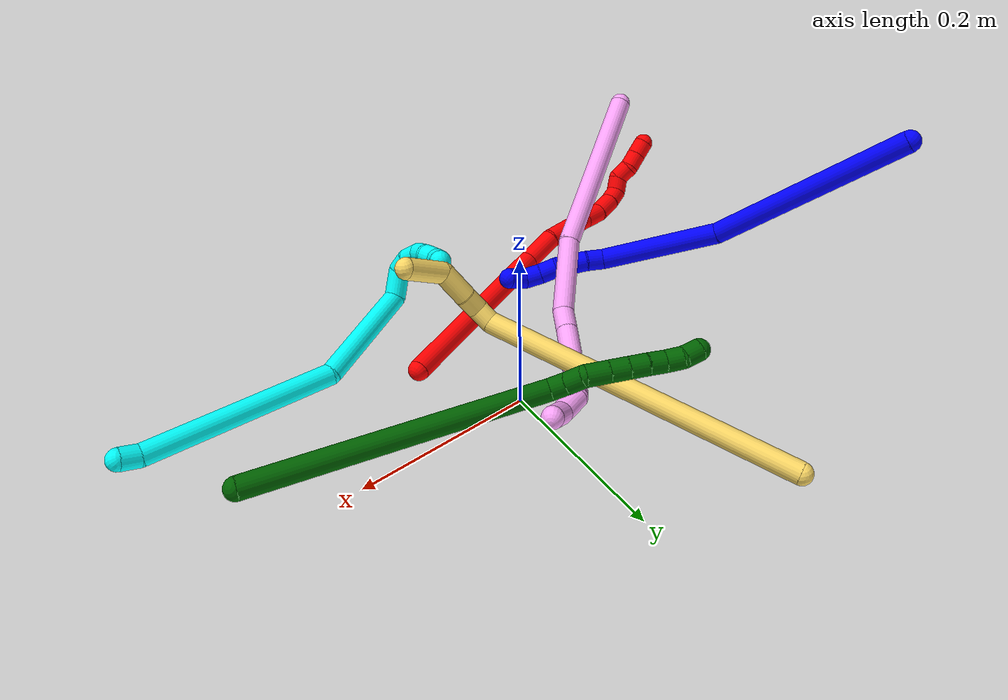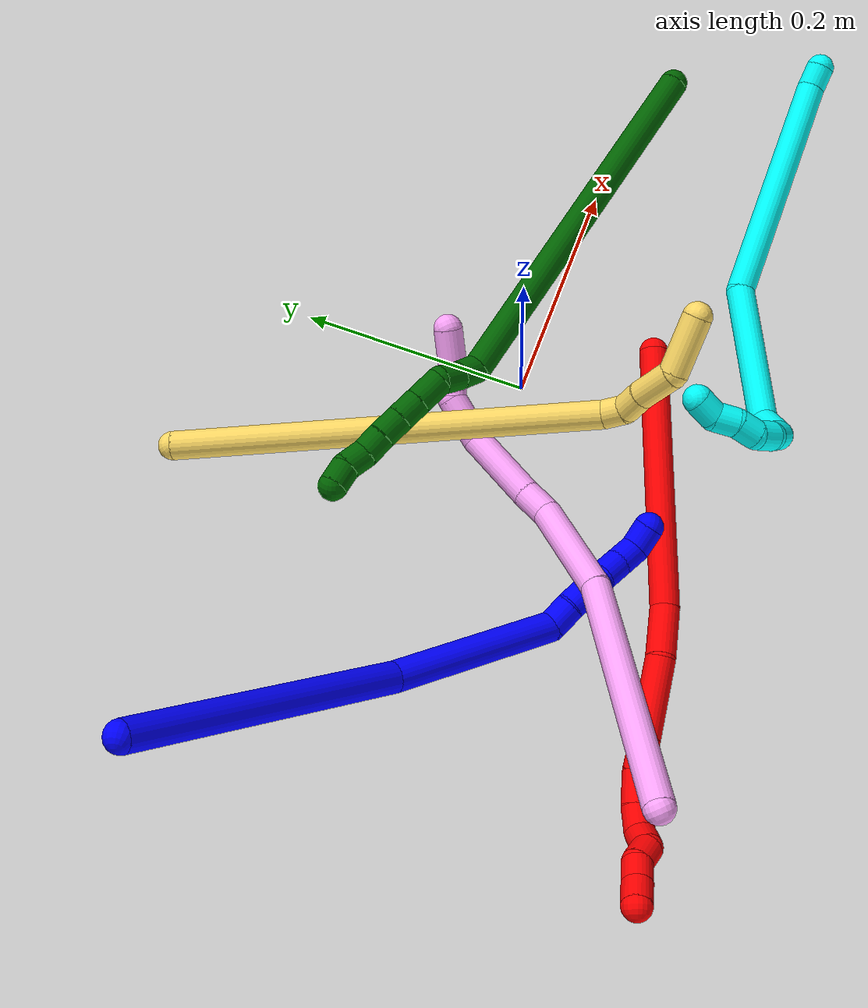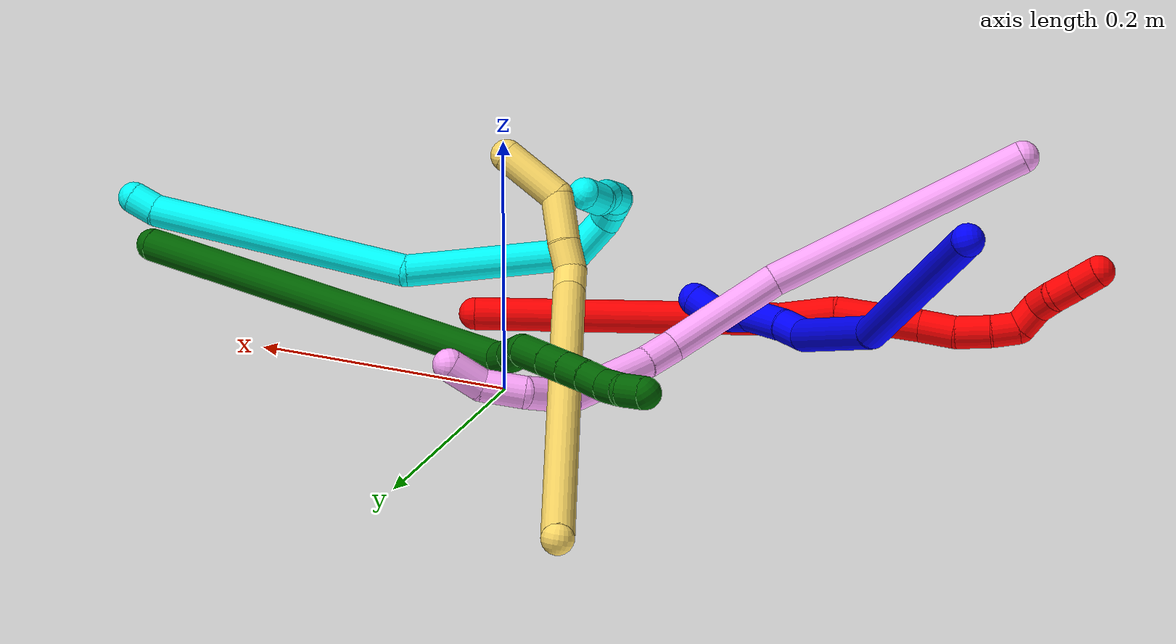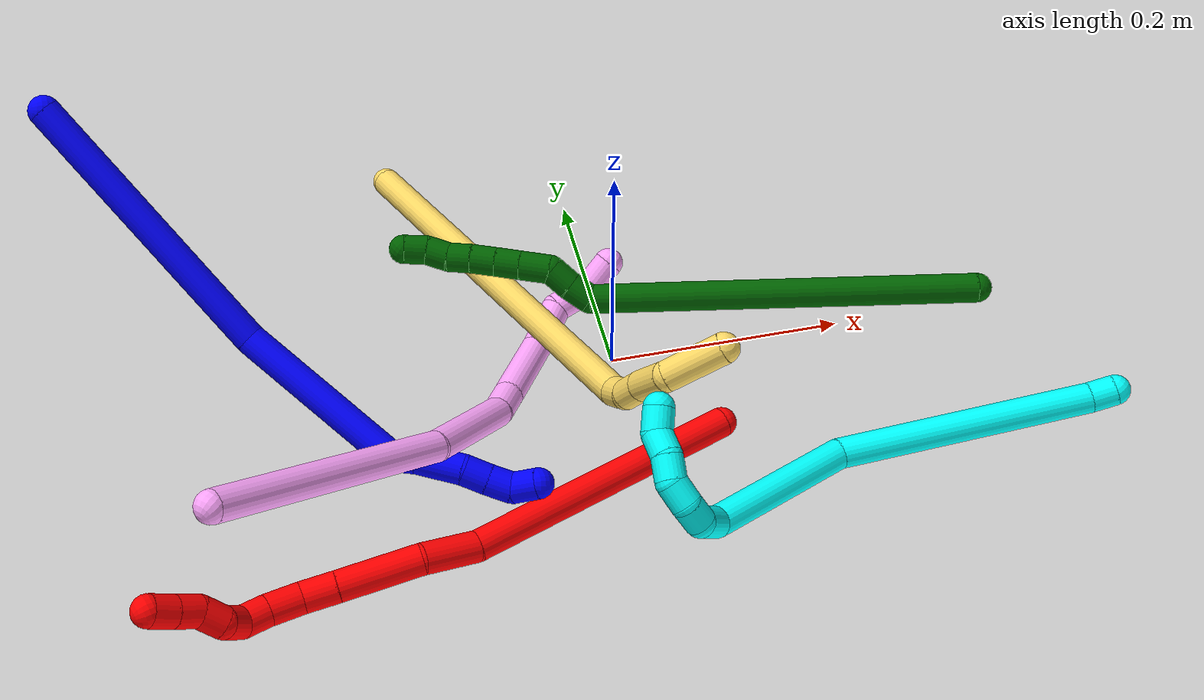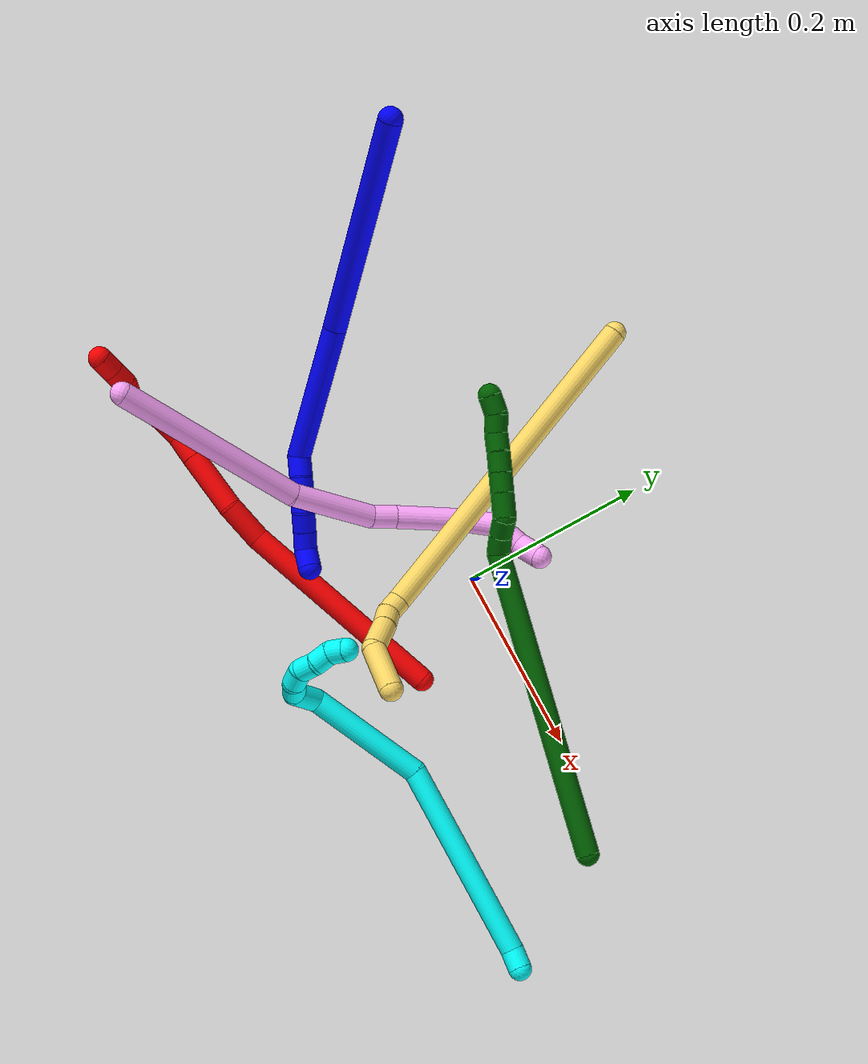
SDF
<sdf version="1.7">
 <world name="default">
  <plugin name="TubeGeneratorPlugin" filename="libtube_generator_plugin.so"/>
  <model name="photoneo_s_sensor">
   <static>1</static>
   <pose>0 0 2 1.57079 1.57079 3.14159</pose>
   <link name="link">
    <inertial><mass>0.1</mass></inertial>
    <sensor name="sensor" type="depth">
     <update_rate>30</update_rate>
     <camera>
      <horizontal_fov>1.22</horizontal_fov>
      <image><width>1920</width><height>1200</height><format>B8G8R8</format></image>
      <clip><near>0.1</near><far>4</far></clip>
      <depth_camera><output>points</output></depth_camera>
     </camera>
     <plugin name="camera_plugin" filename="libgazebo_ros_depth_camera.so">
      <baseline>0.2</baseline>
      <alwaysOn>1</alwaysOn>
      <updateRate>0.0</updateRate>
      <cameraName>camera_ir</cameraName>
      <imageTopicName>/camera/color/image_raw</imageTopicName>
      <cameraInfoTopicName>/camera/color/camera_info</cameraInfoTopicName>
      <depthImageTopicName>/camera/depth/image_raw</depthImageTopicName>
      <depthImageCameraInfoTopicName>/camera/depth/camera_info</depthImageCameraInfoTopicName>
      <pointCloudTopicName>/camera/depth/points</pointCloudTopicName>
      <frameName>fr_optical</frameName>
      <pointCloudCutoff>0.1</pointCloudCutoff>
      <pointCloudCutoffMax>2.0</pointCloudCutoffMax>
      <distortionK1>0</distortionK1>
      <distortionK2>0</distortionK2>
      <distortionK3>0</distortionK3>
      <distortionT1>0</distortionT1>
      <distortionT2>0</distortionT2>
      <CxPrime>0</CxPrime>
      <Cx>0</Cx>
      <Cy>0</Cy>
      <focalLength>0</focalLength>
      <hackBaseline>0</hackBaseline>
     </plugin>
    </sensor>
   </link>
  </model>
  <gravity>0 0 -9.8</gravity>
  <magnetic_field>6e-06 2.3e-05 -4.2e-05</magnetic_field>
  <atmosphere type="adiabatic"/>
  <physics name="default_physics" default="0" type="ode">
   <max_step_size>0.003</max_step_size>
   <real_time_factor>1</real_time_factor>
   <real_time_update_rate>1000</real_time_update_rate>
   <max_contacts>10000</max_contacts>
   <ode>
    <solver>
     <type>quick</type>
     <iters>100</iters>
     <sor>1.3</sor>
     <use_dynamic_moi_rescaling>0</use_dynamic_moi_rescaling>
    </solver>
    <constraints>
     <contact_max_correcting_vel>0</contact_max_correcting_vel>
     <contact_surface_layer>0.001</contact_surface_layer>
     <cfm>0</cfm>
     <erp>0.2</erp>
    </constraints>
   </ode>
  </physics>
  <scene><ambient>0.4 0.4 0.4 1</ambient><background>0.7 0.7 0.7 1</background><shadows>0</shadows></scene>
  <audio><device>default</device></audio>
  <spherical_coordinates>
   <surface_model>EARTH_WGS84</surface_model>
   <latitude_deg>0</latitude_deg>
   <longitude_deg>0</longitude_deg>
   <elevation>0</elevation>
   <heading_deg>0</heading_deg>
  </spherical_coordinates>
  <model name="bin">
   <static>1</static>
   <link name="bottom">
    <collision name="collision-bottom">
     <pose>0 0 -0.01 0 -0 0</pose>
     <geometry><box><size>0.8 0.6 0.02</size></box></geometry>
     <surface>
      <friction><ode><mu>100</mu><mu2>100</mu2></ode></friction>
      <contact><collide_bitmask>65535</collide_bitmask></contact>
     </surface>
    </collision>
   </link>
   <link name="west_wall">
    <collision name="collision-west_wall">
     <pose>-0.41 0 0.1 0 -0 0</pose>
     <geometry><box><size>0.02 0.6 0.2</size></box></geometry>
     <surface>
      <friction><ode><mu>100</mu><mu2>100</mu2></ode></friction>
      <contact><collide_bitmask>65535</collide_bitmask></contact>
     </surface>
    </collision>
   </link>
   <link name="east_wall">
    <collision name="collision-east_wall">
     <pose>0.41 0 0.1 0 -0 0</pose>
     <geometry><box><size>0.02 0.6 0.2</size></box></geometry>
     <surface>
      <friction><ode><mu>100</mu><mu2>100</mu2></ode></friction>
      <contact><collide_bitmask>65535</collide_bitmask></contact>
     </surface>
    </collision>
   </link>
   <link name="south_wall">
    <collision name="collision-south_wall">
     <pose>0 -0.31 0.1 0 -0 0</pose>
     <geometry><box><size>0.8 0.02 0.2</size></box></geometry>
     <surface>
      <friction><ode><mu>100</mu><mu2>100</mu2></ode></friction>
      <contact><collide_bitmask>65535</collide_bitmask></contact>
     </surface>
    </collision>
   </link>
   <link name="north_wall">
    <collision name="collision-north_wall">
     <pose>0 0.31 0.1 0 -0 0</pose>
     <geometry><box><size>0.8 0.02 0.2</size></box></geometry>
     <surface>
      <friction><ode><mu>100</mu><mu2>100</mu2></ode></friction>
      <contact><collide_bitmask>65535</collide_bitmask></contact>
     </surface>
    </collision>
   </link>
  </model>
  <model name="1">
   <static>0</static>
   <link name="1">
    <collision name="collision-cylinder-e_1_1_4">
     <pose>-0.024189 -0.088543 -0.072288 2.25547 -0.208546 -0.434132</pose>
     <geometry><cylinder><radius>0.0125</radius><length>0.233671</length></cylinder></geometry>
     <surface>
      <friction><ode><mu>1.16</mu><mu2>1.16</mu2><slip1>0</slip1><slip2>0</slip2></ode></friction>
      <contact><ode><kp>1e+06</kp><kd>1</kd><max_vel>0</max_vel><min_depth>0.001</min_depth></ode></contact>
     </surface>
    </collision>
    <visual name="visual-cylinder-e_1_1_4">
     <pose>-0.024189 -0.088543 -0.072288 2.25547 -0.208546 -0.434132</pose>
     <geometry><cylinder><radius>0.0125</radius><length>0.233671</length></cylinder></geometry>
     <material><ambient>0 0 1 1</ambient></material>
    </visual>
    <collision name="collision-cylinder-e_2_4_5">
     <pose>-0.043772 -0.233515 -0.189096 2.23876 0.064006 0.131877</pose>
     <geometry><cylinder><radius>0.0125</radius><length>0.144048</length></cylinder></geometry>
     <surface>
      <friction><ode><mu>1.16</mu><mu2>1.16</mu2><slip1>0</slip1><slip2>0</slip2></ode></friction>
      <contact><ode><kp>1e+06</kp><kd>1</kd><max_vel>0</max_vel><min_depth>0.001</min_depth></ode></contact>
     </surface>
    </collision>
    <visual name="visual-cylinder-e_2_4_5">
     <pose>-0.043772 -0.233515 -0.189096 2.23876 0.064006 0.131877</pose>
     <geometry><cylinder><radius>0.0125</radius><length>0.144048</length></cylinder></geometry>
     <material><ambient>0 0 1 1</ambient></material>
    </visual>
    <collision name="collision-cylinder-e_3_5_6">
     <pose>-0.033654 -0.294572 -0.242116 2.6431 0.517645 1.61016</pose>
     <geometry><cylinder><radius>0.0125</radius><length>0.022276</length></cylinder></geometry>
     <surface>
      <friction><ode><mu>1.16</mu><mu2>1.16</mu2><slip1>0</slip1><slip2>0</slip2></ode></friction>
      <contact><ode><kp>1e+06</kp><kd>1</kd><max_vel>0</max_vel><min_depth>0.001</min_depth></ode></contact>
     </surface>
    </collision>
    <visual name="visual-cylinder-e_3_5_6">
     <pose>-0.033654 -0.294572 -0.242116 2.6431 0.517645 1.61016</pose>
     <geometry><cylinder><radius>0.0125</radius><length>0.022276</length></cylinder></geometry>
     <material><ambient>0 0 1 1</ambient></material>
    </visual>
    <collision name="collision-cylinder-e_4_6_7">
     <pose>-0.021465 -0.308376 -0.265575 2.59131 0.363568 1.15434</pose>
     <geometry><cylinder><radius>0.0125</radius><length>0.037552</length></cylinder></geometry>
     <surface>
      <friction><ode><mu>1.16</mu><mu2>1.16</mu2><slip1>0</slip1><slip2>0</slip2></ode></friction>
      <contact><ode><kp>1e+06</kp><kd>1</kd><max_vel>0</max_vel><min_depth>0.001</min_depth></ode></contact>
     </surface>
    </collision>
    <visual name="visual-cylinder-e_4_6_7">
     <pose>-0.021465 -0.308376 -0.265575 2.59131 0.363568 1.15434</pose>
     <geometry><cylinder><radius>0.0125</radius><length>0.037552</length></cylinder></geometry>
     <material><ambient>0 0 1 1</ambient></material>
    </visual>
    <collision name="collision-cylinder-e_5_7_8">
     <pose>-0.013451 -0.322989 -0.289125 2.57746 0.130767 0.444426</pose>
     <geometry><cylinder><radius>0.0125</radius><length>0.02051</length></cylinder></geometry>
     <surface>
      <friction><ode><mu>1.16</mu><mu2>1.16</mu2><slip1>0</slip1><slip2>0</slip2></ode></friction>
      <contact><ode><kp>1e+06</kp><kd>1</kd><max_vel>0</max_vel><min_depth>0.001</min_depth></ode></contact>
     </surface>
    </collision>
    <visual name="visual-cylinder-e_5_7_8">
     <pose>-0.013451 -0.322989 -0.289125 2.57746 0.130767 0.444426</pose>
     <geometry><cylinder><radius>0.0125</radius><length>0.02051</length></cylinder></geometry>
     <material><ambient>0 0 1 1</ambient></material>
    </visual>
    <collision name="collision-cylinder-e_6_8_9">
     <pose>-0.009684 -0.333868 -0.306123 2.56702 0.238052 0.769212</pose>
     <geometry><cylinder><radius>0.0125</radius><length>0.02061</length></cylinder></geometry>
     <surface>
      <friction><ode><mu>1.16</mu><mu2>1.16</mu2><slip1>0</slip1><slip2>0</slip2></ode></friction>
      <contact><ode><kp>1e+06</kp><kd>1</kd><max_vel>0</max_vel><min_depth>0.001</min_depth></ode></contact>
     </surface>
    </collision>
    <visual name="visual-cylinder-e_6_8_9">
     <pose>-0.009684 -0.333868 -0.306123 2.56702 0.238052 0.769212</pose>
     <geometry><cylinder><radius>0.0125</radius><length>0.02061</length></cylinder></geometry>
     <material><ambient>0 0 1 1</ambient></material>
    </visual>
    <collision name="collision-cylinder-e_7_9_2">
     <pose>0.000105 -0.341457 -0.321947 2.8599 0.76134 2.46061</pose>
     <geometry><cylinder><radius>0.0125</radius><length>0.021334</length></cylinder></geometry>
     <surface>
      <friction><ode><mu>1.16</mu><mu2>1.16</mu2><slip1>0</slip1><slip2>0</slip2></ode></friction>
      <contact><ode><kp>1e+06</kp><kd>1</kd><max_vel>0</max_vel><min_depth>0.001</min_depth></ode></contact>
     </surface>
    </collision>
    <visual name="visual-cylinder-e_7_9_2">
     <pose>0.000105 -0.341457 -0.321947 2.8599 0.76134 2.46061</pose>
     <geometry><cylinder><radius>0.0125</radius><length>0.021334</length></cylinder></geometry>
     <material><ambient>0 0 1 1</ambient></material>
    </visual>
    <collision name="collision-sphere-2">
     <pose>0.007464 -0.343603 -0.329364 0 -0 0</pose>
     <geometry><sphere><radius>0.0125</radius></sphere></geometry>
     <surface>
      <friction><ode><mu>1.16</mu><mu2>1.16</mu2><slip1>0</slip1><slip2>0</slip2></ode></friction>
      <contact><ode><kp>1e+06</kp><kd>1</kd><max_vel>0</max_vel><min_depth>0.001</min_depth></ode></contact>
     </surface>
    </collision>
    <visual name="visual-sphere-2">
     <pose>0.007464 -0.343603 -0.329364 0 -0 0</pose>
     <geometry><sphere><radius>0.0125</radius></sphere></geometry>
     <material><ambient>0 0 1 1</ambient></material>
    </visual>
    <collision name="collision-sphere-9">
     <pose>-0.007254 -0.33931 -0.314529 0 -0 0</pose>
     <geometry><sphere><radius>0.0125</radius></sphere></geometry>
     <surface>
      <friction><ode><mu>1.16</mu><mu2>1.16</mu2><slip1>0</slip1><slip2>0</slip2></ode></friction>
      <contact><ode><kp>1e+06</kp><kd>1</kd><max_vel>0</max_vel><min_depth>0.001</min_depth></ode></contact>
     </surface>
    </collision>
    <visual name="visual-sphere-9">
     <pose>-0.007254 -0.33931 -0.314529 0 -0 0</pose>
     <geometry><sphere><radius>0.0125</radius></sphere></geometry>
     <material><ambient>0 0 1 1</ambient></material>
    </visual>
    <collision name="collision-sphere-4">
     <pose>-0.048379 -0.177086 -0.144577 0 -0 0</pose>
     <geometry><sphere><radius>0.0125</radius></sphere></geometry>
     <surface>
      <friction><ode><mu>1.16</mu><mu2>1.16</mu2><slip1>0</slip1><slip2>0</slip2></ode></friction>
      <contact><ode><kp>1e+06</kp><kd>1</kd><max_vel>0</max_vel><min_depth>0.001</min_depth></ode></contact>
     </surface>
    </collision>
    <visual name="visual-sphere-4">
     <pose>-0.048379 -0.177086 -0.144577 0 -0 0</pose>
     <geometry><sphere><radius>0.0125</radius></sphere></geometry>
     <material><ambient>0 0 1 1</ambient></material>
    </visual>
    <collision name="collision-sphere-1">
     <geometry><sphere><radius>0.0125</radius></sphere></geometry>
     <surface>
      <friction><ode><mu>1.16</mu><mu2>1.16</mu2><slip1>0</slip1><slip2>0</slip2></ode></friction>
      <contact><ode><kp>1e+06</kp><kd>1</kd><max_vel>0</max_vel><min_depth>0.001</min_depth></ode></contact>
     </surface>
    </collision>
    <visual name="visual-sphere-1">
     <geometry><sphere><radius>0.0125</radius></sphere></geometry>
     <material><ambient>0 0 1 1</ambient></material>
    </visual>
    <collision name="collision-sphere-8">
     <pose>-0.012114 -0.328425 -0.297717 0 -0 0</pose>
     <geometry><sphere><radius>0.0125</radius></sphere></geometry>
     <surface>
      <friction><ode><mu>1.16</mu><mu2>1.16</mu2><slip1>0</slip1><slip2>0</slip2></ode></friction>
      <contact><ode><kp>1e+06</kp><kd>1</kd><max_vel>0</max_vel><min_depth>0.001</min_depth></ode></contact>
     </surface>
    </collision>
    <visual name="visual-sphere-8">
     <pose>-0.012114 -0.328425 -0.297717 0 -0 0</pose>
     <geometry><sphere><radius>0.0125</radius></sphere></geometry>
     <material><ambient>0 0 1 1</ambient></material>
    </visual>
    <collision name="collision-sphere-5">
     <pose>-0.039165 -0.289944 -0.233615 0 -0 0</pose>
     <geometry><sphere><radius>0.0125</radius></sphere></geometry>
     <surface>
      <friction><ode><mu>1.16</mu><mu2>1.16</mu2><slip1>0</slip1><slip2>0</slip2></ode></friction>
      <contact><ode><kp>1e+06</kp><kd>1</kd><max_vel>0</max_vel><min_depth>0.001</min_depth></ode></contact>
     </surface>
    </collision>
    <visual name="visual-sphere-5">
     <pose>-0.039165 -0.289944 -0.233615 0 -0 0</pose>
     <geometry><sphere><radius>0.0125</radius></sphere></geometry>
     <material><ambient>0 0 1 1</ambient></material>
    </visual>
    <collision name="collision-sphere-6">
     <pose>-0.028142 -0.299199 -0.250617 0 -0 0</pose>
     <geometry><sphere><radius>0.0125</radius></sphere></geometry>
     <surface>
      <friction><ode><mu>1.16</mu><mu2>1.16</mu2><slip1>0</slip1><slip2>0</slip2></ode></friction>
      <contact><ode><kp>1e+06</kp><kd>1</kd><max_vel>0</max_vel><min_depth>0.001</min_depth></ode></contact>
     </surface>
    </collision>
    <visual name="visual-sphere-6">
     <pose>-0.028142 -0.299199 -0.250617 0 -0 0</pose>
     <geometry><sphere><radius>0.0125</radius></sphere></geometry>
     <material><ambient>0 0 1 1</ambient></material>
    </visual>
    <collision name="collision-sphere-7">
     <pose>-0.014788 -0.317552 -0.280533 0 -0 0</pose>
     <geometry><sphere><radius>0.0125</radius></sphere></geometry>
     <surface>
      <friction><ode><mu>1.16</mu><mu2>1.16</mu2><slip1>0</slip1><slip2>0</slip2></ode></friction>
      <contact><ode><kp>1e+06</kp><kd>1</kd><max_vel>0</max_vel><min_depth>0.001</min_depth></ode></contact>
     </surface>
    </collision>
    <visual name="visual-sphere-7">
     <pose>-0.014788 -0.317552 -0.280533 0 -0 0</pose>
     <geometry><sphere><radius>0.0125</radius></sphere></geometry>
     <material><ambient>0 0 1 1</ambient></material>
    </visual>
    <inertial>
     <pose>-0.027973 -0.186518 -0.157208 0 -0 0</pose>
     <mass>0.5</mass>
     <inertia>
      <ixx>0.000809</ixx>
      <ixy>0</ixy>
      <ixz>0</ixz>
      <iyy>-0.001124</iyy>
      <iyz>0</iyz>
      <izz>0.001193</izz>
     </inertia>
    </inertial>
   </link>
   <pose>-0.419753 0.131205 0.240504 0.697963 -1.09929 -0.582791</pose>
  </model>
  <model name="2">
   <static>0</static>
   <link name="2">
    <collision name="collision-cylinder-e_1_1_4">
     <pose>0.002897 -0.000135 0.115991 0.001164 0.024974 1.5e-05</pose>
     <geometry><cylinder><radius>0.0125</radius><length>0.232055</length></cylinder></geometry>
     <surface>
      <friction><ode><mu>1.16</mu><mu2>1.16</mu2><slip1>0</slip1><slip2>0</slip2></ode></friction>
      <contact><ode><kp>1e+06</kp><kd>1</kd><max_vel>0</max_vel><min_depth>0.001</min_depth></ode></contact>
     </surface>
    </collision>
    <visual name="visual-cylinder-e_1_1_4">
     <pose>0.002897 -0.000135 0.115991 0.001164 0.024974 1.5e-05</pose>
     <geometry><cylinder><radius>0.0125</radius><length>0.232055</length></cylinder></geometry>
     <material><ambient>1 0 0 1</ambient></material>
    </visual>
    <collision name="collision-cylinder-e_2_4_5">
     <pose>0.001091 -0.001725 0.254001 0.065966 -0.209993 -0.006954</pose>
     <geometry><cylinder><radius>0.0125</radius><length>0.045125</length></cylinder></geometry>
     <surface>
      <friction><ode><mu>1.16</mu><mu2>1.16</mu2><slip1>0</slip1><slip2>0</slip2></ode></friction>
      <contact><ode><kp>1e+06</kp><kd>1</kd><max_vel>0</max_vel><min_depth>0.001</min_depth></ode></contact>
     </surface>
    </collision>
    <visual name="visual-cylinder-e_2_4_5">
     <pose>0.001091 -0.001725 0.254001 0.065966 -0.209993 -0.006954</pose>
     <geometry><cylinder><radius>0.0125</radius><length>0.045125</length></cylinder></geometry>
     <material><ambient>1 0 0 1</ambient></material>
    </visual>
    <collision name="collision-cylinder-e_3_5_6">
     <pose>-0.00352 -0.010638 0.30811 0.228377 0.002788 0.00032</pose>
     <geometry><cylinder><radius>0.0125</radius><length>0.065891</length></cylinder></geometry>
     <surface>
      <friction><ode><mu>1.16</mu><mu2>1.16</mu2><slip1>0</slip1><slip2>0</slip2></ode></friction>
      <contact><ode><kp>1e+06</kp><kd>1</kd><max_vel>0</max_vel><min_depth>0.001</min_depth></ode></contact>
     </surface>
    </collision>
    <visual name="visual-cylinder-e_3_5_6">
     <pose>-0.00352 -0.010638 0.30811 0.228377 0.002788 0.00032</pose>
     <geometry><cylinder><radius>0.0125</radius><length>0.065891</length></cylinder></geometry>
     <material><ambient>1 0 0 1</ambient></material>
    </visual>
    <collision name="collision-cylinder-e_4_6_7">
     <pose>-0.003243 -0.021649 0.353381 0.263249 0.013529 0.001791</pose>
     <geometry><cylinder><radius>0.0125</radius><length>0.027306</length></cylinder></geometry>
     <surface>
      <friction><ode><mu>1.16</mu><mu2>1.16</mu2><slip1>0</slip1><slip2>0</slip2></ode></friction>
      <contact><ode><kp>1e+06</kp><kd>1</kd><max_vel>0</max_vel><min_depth>0.001</min_depth></ode></contact>
     </surface>
    </collision>
    <visual name="visual-cylinder-e_4_6_7">
     <pose>-0.003243 -0.021649 0.353381 0.263249 0.013529 0.001791</pose>
     <geometry><cylinder><radius>0.0125</radius><length>0.027306</length></cylinder></geometry>
     <material><ambient>1 0 0 1</ambient></material>
    </visual>
    <collision name="collision-cylinder-e_5_7_8">
     <pose>-0.004166 -0.025848 0.380162 0.047481 -0.081122 -0.001927</pose>
     <geometry><cylinder><radius>0.0125</radius><length>0.02732</length></cylinder></geometry>
     <surface>
      <friction><ode><mu>1.16</mu><mu2>1.16</mu2><slip1>0</slip1><slip2>0</slip2></ode></friction>
      <contact><ode><kp>1e+06</kp><kd>1</kd><max_vel>0</max_vel><min_depth>0.001</min_depth></ode></contact>
     </surface>
    </collision>
    <visual name="visual-cylinder-e_5_7_8">
     <pose>-0.004166 -0.025848 0.380162 0.047481 -0.081122 -0.001927</pose>
     <geometry><cylinder><radius>0.0125</radius><length>0.02732</length></cylinder></geometry>
     <material><ambient>1 0 0 1</ambient></material>
    </visual>
    <collision name="collision-cylinder-e_6_8_9">
     <pose>-0.006133 -0.025329 0.40424 -0.110704 -0.08142 0.004514</pose>
     <geometry><cylinder><radius>0.0125</radius><length>0.021156</length></cylinder></geometry>
     <surface>
      <friction><ode><mu>1.16</mu><mu2>1.16</mu2><slip1>0</slip1><slip2>0</slip2></ode></friction>
      <contact><ode><kp>1e+06</kp><kd>1</kd><max_vel>0</max_vel><min_depth>0.001</min_depth></ode></contact>
     </surface>
    </collision>
    <visual name="visual-cylinder-e_6_8_9">
     <pose>-0.006133 -0.025329 0.40424 -0.110704 -0.08142 0.004514</pose>
     <geometry><cylinder><radius>0.0125</radius><length>0.021156</length></cylinder></geometry>
     <material><ambient>1 0 0 1</ambient></material>
    </visual>
    <collision name="collision-cylinder-e_7_9_10">
     <pose>-0.01349 -0.019693 0.421527 -0.581126 -0.673298 0.208542</pose>
     <geometry><cylinder><radius>0.0125</radius><length>0.020839</length></cylinder></geometry>
     <surface>
      <friction><ode><mu>1.16</mu><mu2>1.16</mu2><slip1>0</slip1><slip2>0</slip2></ode></friction>
      <contact><ode><kp>1e+06</kp><kd>1</kd><max_vel>0</max_vel><min_depth>0.001</min_depth></ode></contact>
     </surface>
    </collision>
    <visual name="visual-cylinder-e_7_9_10">
     <pose>-0.01349 -0.019693 0.421527 -0.581126 -0.673298 0.208542</pose>
     <geometry><cylinder><radius>0.0125</radius><length>0.020839</length></cylinder></geometry>
     <material><ambient>1 0 0 1</ambient></material>
    </visual>
    <collision name="collision-cylinder-e_8_10_11">
     <pose>-0.027448 -0.017473 0.434833 0.333658 -0.826094 -0.147334</pose>
     <geometry><cylinder><radius>0.0125</radius><length>0.020293</length></cylinder></geometry>
     <surface>
      <friction><ode><mu>1.16</mu><mu2>1.16</mu2><slip1>0</slip1><slip2>0</slip2></ode></friction>
      <contact><ode><kp>1e+06</kp><kd>1</kd><max_vel>0</max_vel><min_depth>0.001</min_depth></ode></contact>
     </surface>
    </collision>
    <visual name="visual-cylinder-e_8_10_11">
     <pose>-0.027448 -0.017473 0.434833 0.333658 -0.826094 -0.147334</pose>
     <geometry><cylinder><radius>0.0125</radius><length>0.020293</length></cylinder></geometry>
     <material><ambient>1 0 0 1</ambient></material>
    </visual>
    <collision name="collision-cylinder-e_9_11_12">
     <pose>-0.040061 -0.018641 0.44984 -0.126734 -0.540899 0.03518</pose>
     <geometry><cylinder><radius>0.0125</radius><length>0.020014</length></cylinder></geometry>
     <surface>
      <friction><ode><mu>1.16</mu><mu2>1.16</mu2><slip1>0</slip1><slip2>0</slip2></ode></friction>
      <contact><ode><kp>1e+06</kp><kd>1</kd><max_vel>0</max_vel><min_depth>0.001</min_depth></ode></contact>
     </surface>
    </collision>
    <visual name="visual-cylinder-e_9_11_12">
     <pose>-0.040061 -0.018641 0.44984 -0.126734 -0.540899 0.03518</pose>
     <geometry><cylinder><radius>0.0125</radius><length>0.020014</length></cylinder></geometry>
     <material><ambient>1 0 0 1</ambient></material>
    </visual>
    <collision name="collision-cylinder-e_10_12_2">
     <pose>-0.050627 -0.016585 0.466702 -0.115886 -0.571974 0.034111</pose>
     <geometry><cylinder><radius>0.0125</radius><length>0.020003</length></cylinder></geometry>
     <surface>
      <friction><ode><mu>1.16</mu><mu2>1.16</mu2><slip1>0</slip1><slip2>0</slip2></ode></friction>
      <contact><ode><kp>1e+06</kp><kd>1</kd><max_vel>0</max_vel><min_depth>0.001</min_depth></ode></contact>
     </surface>
    </collision>
    <visual name="visual-cylinder-e_10_12_2">
     <pose>-0.050627 -0.016585 0.466702 -0.115886 -0.571974 0.034111</pose>
     <geometry><cylinder><radius>0.0125</radius><length>0.020003</length></cylinder></geometry>
     <material><ambient>1 0 0 1</ambient></material>
    </visual>
    <collision name="collision-sphere-2">
     <pose>-0.056041 -0.015612 0.475055 0 -0 0</pose>
     <geometry><sphere><radius>0.0125</radius></sphere></geometry>
     <surface>
      <friction><ode><mu>1.16</mu><mu2>1.16</mu2><slip1>0</slip1><slip2>0</slip2></ode></friction>
      <contact><ode><kp>1e+06</kp><kd>1</kd><max_vel>0</max_vel><min_depth>0.001</min_depth></ode></contact>
     </surface>
    </collision>
    <visual name="visual-sphere-2">
     <pose>-0.056041 -0.015612 0.475055 0 -0 0</pose>
     <geometry><sphere><radius>0.0125</radius></sphere></geometry>
     <material><ambient>1 0 0 1</ambient></material>
    </visual>
    <collision name="collision-sphere-12">
     <pose>-0.045214 -0.017557 0.458349 0 -0 0</pose>
     <geometry><sphere><radius>0.0125</radius></sphere></geometry>
     <surface>
      <friction><ode><mu>1.16</mu><mu2>1.16</mu2><slip1>0</slip1><slip2>0</slip2></ode></friction>
      <contact><ode><kp>1e+06</kp><kd>1</kd><max_vel>0</max_vel><min_depth>0.001</min_depth></ode></contact>
     </surface>
    </collision>
    <visual name="visual-sphere-12">
     <pose>-0.045214 -0.017557 0.458349 0 -0 0</pose>
     <geometry><sphere><radius>0.0125</radius></sphere></geometry>
     <material><ambient>1 0 0 1</ambient></material>
    </visual>
    <collision name="collision-sphere-11">
     <pose>-0.034908 -0.019725 0.44133 0 -0 0</pose>
     <geometry><sphere><radius>0.0125</radius></sphere></geometry>
     <surface>
      <friction><ode><mu>1.16</mu><mu2>1.16</mu2><slip1>0</slip1><slip2>0</slip2></ode></friction>
      <contact><ode><kp>1e+06</kp><kd>1</kd><max_vel>0</max_vel><min_depth>0.001</min_depth></ode></contact>
     </surface>
    </collision>
    <visual name="visual-sphere-11">
     <pose>-0.034908 -0.019725 0.44133 0 -0 0</pose>
     <geometry><sphere><radius>0.0125</radius></sphere></geometry>
     <material><ambient>1 0 0 1</ambient></material>
    </visual>
    <collision name="collision-sphere-10">
     <pose>-0.019987 -0.015221 0.428335 0 -0 0</pose>
     <geometry><sphere><radius>0.0125</radius></sphere></geometry>
     <surface>
      <friction><ode><mu>1.16</mu><mu2>1.16</mu2><slip1>0</slip1><slip2>0</slip2></ode></friction>
      <contact><ode><kp>1e+06</kp><kd>1</kd><max_vel>0</max_vel><min_depth>0.001</min_depth></ode></contact>
     </surface>
    </collision>
    <visual name="visual-sphere-10">
     <pose>-0.019987 -0.015221 0.428335 0 -0 0</pose>
     <geometry><sphere><radius>0.0125</radius></sphere></geometry>
     <material><ambient>1 0 0 1</ambient></material>
    </visual>
    <collision name="collision-sphere-9">
     <pose>-0.006993 -0.024164 0.414718 0 -0 0</pose>
     <geometry><sphere><radius>0.0125</radius></sphere></geometry>
     <surface>
      <friction><ode><mu>1.16</mu><mu2>1.16</mu2><slip1>0</slip1><slip2>0</slip2></ode></friction>
      <contact><ode><kp>1e+06</kp><kd>1</kd><max_vel>0</max_vel><min_depth>0.001</min_depth></ode></contact>
     </surface>
    </collision>
    <visual name="visual-sphere-9">
     <pose>-0.006993 -0.024164 0.414718 0 -0 0</pose>
     <geometry><sphere><radius>0.0125</radius></sphere></geometry>
     <material><ambient>1 0 0 1</ambient></material>
    </visual>
    <collision name="collision-sphere-4">
     <pose>0.005795 -0.00027 0.231982 0 -0 0</pose>
     <geometry><sphere><radius>0.0125</radius></sphere></geometry>
     <surface>
      <friction><ode><mu>1.16</mu><mu2>1.16</mu2><slip1>0</slip1><slip2>0</slip2></ode></friction>
      <contact><ode><kp>1e+06</kp><kd>1</kd><max_vel>0</max_vel><min_depth>0.001</min_depth></ode></contact>
     </surface>
    </collision>
    <visual name="visual-sphere-4">
     <pose>0.005795 -0.00027 0.231982 0 -0 0</pose>
     <geometry><sphere><radius>0.0125</radius></sphere></geometry>
     <material><ambient>1 0 0 1</ambient></material>
    </visual>
    <collision name="collision-sphere-1">
     <geometry><sphere><radius>0.0125</radius></sphere></geometry>
     <surface>
      <friction><ode><mu>1.16</mu><mu2>1.16</mu2><slip1>0</slip1><slip2>0</slip2></ode></friction>
      <contact><ode><kp>1e+06</kp><kd>1</kd><max_vel>0</max_vel><min_depth>0.001</min_depth></ode></contact>
     </surface>
    </collision>
    <visual name="visual-sphere-1">
     <geometry><sphere><radius>0.0125</radius></sphere></geometry>
     <material><ambient>1 0 0 1</ambient></material>
    </visual>
    <collision name="collision-sphere-8">
     <pose>-0.005272 -0.026494 0.393762 0 -0 0</pose>
     <geometry><sphere><radius>0.0125</radius></sphere></geometry>
     <surface>
      <friction><ode><mu>1.16</mu><mu2>1.16</mu2><slip1>0</slip1><slip2>0</slip2></ode></friction>
      <contact><ode><kp>1e+06</kp><kd>1</kd><max_vel>0</max_vel><min_depth>0.001</min_depth></ode></contact>
     </surface>
    </collision>
    <visual name="visual-sphere-8">
     <pose>-0.005272 -0.026494 0.393762 0 -0 0</pose>
     <geometry><sphere><radius>0.0125</radius></sphere></geometry>
     <material><ambient>1 0 0 1</ambient></material>
    </visual>
    <collision name="collision-sphere-5">
     <pose>-0.003612 -0.003179 0.27602 0 -0 0</pose>
     <geometry><sphere><radius>0.0125</radius></sphere></geometry>
     <surface>
      <friction><ode><mu>1.16</mu><mu2>1.16</mu2><slip1>0</slip1><slip2>0</slip2></ode></friction>
      <contact><ode><kp>1e+06</kp><kd>1</kd><max_vel>0</max_vel><min_depth>0.001</min_depth></ode></contact>
     </surface>
    </collision>
    <visual name="visual-sphere-5">
     <pose>-0.003612 -0.003179 0.27602 0 -0 0</pose>
     <geometry><sphere><radius>0.0125</radius></sphere></geometry>
     <material><ambient>1 0 0 1</ambient></material>
    </visual>
    <collision name="collision-sphere-6">
     <pose>-0.003428 -0.018097 0.3402 0 -0 0</pose>
     <geometry><sphere><radius>0.0125</radius></sphere></geometry>
     <surface>
      <friction><ode><mu>1.16</mu><mu2>1.16</mu2><slip1>0</slip1><slip2>0</slip2></ode></friction>
      <contact><ode><kp>1e+06</kp><kd>1</kd><max_vel>0</max_vel><min_depth>0.001</min_depth></ode></contact>
     </surface>
    </collision>
    <visual name="visual-sphere-6">
     <pose>-0.003428 -0.018097 0.3402 0 -0 0</pose>
     <geometry><sphere><radius>0.0125</radius></sphere></geometry>
     <material><ambient>1 0 0 1</ambient></material>
    </visual>
    <collision name="collision-sphere-7">
     <pose>-0.003059 -0.025201 0.366562 0 -0 0</pose>
     <geometry><sphere><radius>0.0125</radius></sphere></geometry>
     <surface>
      <friction><ode><mu>1.16</mu><mu2>1.16</mu2><slip1>0</slip1><slip2>0</slip2></ode></friction>
      <contact><ode><kp>1e+06</kp><kd>1</kd><max_vel>0</max_vel><min_depth>0.001</min_depth></ode></contact>
     </surface>
    </collision>
    <visual name="visual-sphere-7">
     <pose>-0.003059 -0.025201 0.366562 0 -0 0</pose>
     <geometry><sphere><radius>0.0125</radius></sphere></geometry>
     <material><ambient>1 0 0 1</ambient></material>
    </visual>
    <inertial>
     <pose>-0.00499 -0.008226 0.246427 0 -0 0</pose>
     <mass>0.5</mass>
     <inertia>
      <ixx>0.001093</ixx>
      <ixy>0</ixy>
      <ixz>0</ixz>
      <iyy>0.001097</iyy>
      <iyz>0</iyz>
      <izz>2.5e-05</izz>
     </inertia>
    </inertial>
   </link>
   <pose>0.068381 -0.098591 0.011484 1.49309 1.243 -1.29449</pose>
  </model>
  <model name="3">
   <static>0</static>
   <link name="3">
    <collision name="collision-cylinder-e_1_1_4">
     <pose>-0.007493 -0.007015 -0.003007 1.97574 -0.776158 -1.11001</pose>
     <geometry><cylinder><radius>0.0125</radius><length>0.021391</length></cylinder></geometry>
     <surface>
      <friction><ode><mu>1.16</mu><mu2>1.16</mu2><slip1>0</slip1><slip2>0</slip2></ode></friction>
      <contact><ode><kp>1e+06</kp><kd>1</kd><max_vel>0</max_vel><min_depth>0.001</min_depth></ode></contact>
     </surface>
    </collision>
    <visual name="visual-cylinder-e_1_1_4">
     <pose>-0.007493 -0.007015 -0.003007 1.97574 -0.776158 -1.11001</pose>
     <geometry><cylinder><radius>0.0125</radius><length>0.021391</length></cylinder></geometry>
     <material><ambient>0.003922 1 0.996078 1</ambient></material>
    </visual>
    <collision name="collision-cylinder-e_2_4_5">
     <pose>-0.099328 -0.061717 -0.051273 2.33008 -0.908682 -1.69878</pose>
     <geometry><cylinder><radius>0.0125</radius><length>0.213879</length></cylinder></geometry>
     <surface>
      <friction><ode><mu>1.16</mu><mu2>1.16</mu2><slip1>0</slip1><slip2>0</slip2></ode></friction>
      <contact><ode><kp>1e+06</kp><kd>1</kd><max_vel>0</max_vel><min_depth>0.001</min_depth></ode></contact>
     </surface>
    </collision>
    <visual name="visual-cylinder-e_2_4_5">
     <pose>-0.099328 -0.061717 -0.051273 2.33008 -0.908682 -1.69878</pose>
     <geometry><cylinder><radius>0.0125</radius><length>0.213879</length></cylinder></geometry>
     <material><ambient>0.003922 1 0.996078 1</ambient></material>
    </visual>
    <collision name="collision-cylinder-e_3_5_6">
     <pose>-0.246904 -0.112602 -0.113702 2.95745 -1.3013 -2.90019</pose>
     <geometry><cylinder><radius>0.0125</radius><length>0.131203</length></cylinder></geometry>
     <surface>
      <friction><ode><mu>1.16</mu><mu2>1.16</mu2><slip1>0</slip1><slip2>0</slip2></ode></friction>
      <contact><ode><kp>1e+06</kp><kd>1</kd><max_vel>0</max_vel><min_depth>0.001</min_depth></ode></contact>
     </surface>
    </collision>
    <visual name="visual-cylinder-e_3_5_6">
     <pose>-0.246904 -0.112602 -0.113702 2.95745 -1.3013 -2.90019</pose>
     <geometry><cylinder><radius>0.0125</radius><length>0.131203</length></cylinder></geometry>
     <material><ambient>0.003922 1 0.996078 1</ambient></material>
    </visual>
    <collision name="collision-cylinder-e_4_6_7">
     <pose>-0.321161 -0.106373 -0.139264 -2.29811 -0.717962 1.39303</pose>
     <geometry><cylinder><radius>0.0125</radius><length>0.033513</length></cylinder></geometry>
     <surface>
      <friction><ode><mu>1.16</mu><mu2>1.16</mu2><slip1>0</slip1><slip2>0</slip2></ode></friction>
      <contact><ode><kp>1e+06</kp><kd>1</kd><max_vel>0</max_vel><min_depth>0.001</min_depth></ode></contact>
     </surface>
    </collision>
    <visual name="visual-cylinder-e_4_6_7">
     <pose>-0.321161 -0.106373 -0.139264 -2.29811 -0.717962 1.39303</pose>
     <geometry><cylinder><radius>0.0125</radius><length>0.033513</length></cylinder></geometry>
     <material><ambient>0.003922 1 0.996078 1</ambient></material>
    </visual>
    <collision name="collision-cylinder-e_5_7_8">
     <pose>-0.333833 -0.094509 -0.157218 -2.89204 -0.165556 1.16882</pose>
     <geometry><cylinder><radius>0.0125</radius><length>0.020011</length></cylinder></geometry>
     <surface>
      <friction><ode><mu>1.16</mu><mu2>1.16</mu2><slip1>0</slip1><slip2>0</slip2></ode></friction>
      <contact><ode><kp>1e+06</kp><kd>1</kd><max_vel>0</max_vel><min_depth>0.001</min_depth></ode></contact>
     </surface>
    </collision>
    <visual name="visual-cylinder-e_5_7_8">
     <pose>-0.333833 -0.094509 -0.157218 -2.89204 -0.165556 1.16882</pose>
     <geometry><cylinder><radius>0.0125</radius><length>0.020011</length></cylinder></geometry>
     <material><ambient>0.003922 1 0.996078 1</ambient></material>
    </visual>
    <collision name="collision-cylinder-e_6_8_9">
     <pose>-0.33459 -0.092971 -0.176701 3.0512 0.089276 1.55841</pose>
     <geometry><cylinder><radius>0.0125</radius><length>0.020001</length></cylinder></geometry>
     <surface>
      <friction><ode><mu>1.16</mu><mu2>1.16</mu2><slip1>0</slip1><slip2>0</slip2></ode></friction>
      <contact><ode><kp>1e+06</kp><kd>1</kd><max_vel>0</max_vel><min_depth>0.001</min_depth></ode></contact>
     </surface>
    </collision>
    <visual name="visual-cylinder-e_6_8_9">
     <pose>-0.33459 -0.092971 -0.176701 3.0512 0.089276 1.55841</pose>
     <geometry><cylinder><radius>0.0125</radius><length>0.020001</length></cylinder></geometry>
     <material><ambient>0.003922 1 0.996078 1</ambient></material>
    </visual>
    <collision name="collision-cylinder-e_7_9_10">
     <pose>-0.327685 -0.095342 -0.194475 2.95631 0.645172 2.59939</pose>
     <geometry><cylinder><radius>0.0125</radius><length>0.02</length></cylinder></geometry>
     <surface>
      <friction><ode><mu>1.16</mu><mu2>1.16</mu2><slip1>0</slip1><slip2>0</slip2></ode></friction>
      <contact><ode><kp>1e+06</kp><kd>1</kd><max_vel>0</max_vel><min_depth>0.001</min_depth></ode></contact>
     </surface>
    </collision>
    <visual name="visual-cylinder-e_7_9_10">
     <pose>-0.327685 -0.095342 -0.194475 2.95631 0.645172 2.59939</pose>
     <geometry><cylinder><radius>0.0125</radius><length>0.02</length></cylinder></geometry>
     <material><ambient>0.003922 1 0.996078 1</ambient></material>
    </visual>
    <collision name="collision-cylinder-e_8_10_11">
     <pose>-0.316767 -0.101216 -0.209849 2.6121 0.512636 1.53694</pose>
     <geometry><cylinder><radius>0.0125</radius><length>0.02</length></cylinder></geometry>
     <surface>
      <friction><ode><mu>1.16</mu><mu2>1.16</mu2><slip1>0</slip1><slip2>0</slip2></ode></friction>
      <contact><ode><kp>1e+06</kp><kd>1</kd><max_vel>0</max_vel><min_depth>0.001</min_depth></ode></contact>
     </surface>
    </collision>
    <visual name="visual-cylinder-e_8_10_11">
     <pose>-0.316767 -0.101216 -0.209849 2.6121 0.512636 1.53694</pose>
     <geometry><cylinder><radius>0.0125</radius><length>0.02</length></cylinder></geometry>
     <material><ambient>0.003922 1 0.996078 1</ambient></material>
    </visual>
    <collision name="collision-cylinder-e_9_11_2">
     <pose>-0.304457 -0.105515 -0.22409 -3.12641 0.833863 -3.10731</pose>
     <geometry><cylinder><radius>0.0125</radius><length>0.020001</length></cylinder></geometry>
     <surface>
      <friction><ode><mu>1.16</mu><mu2>1.16</mu2><slip1>0</slip1><slip2>0</slip2></ode></friction>
      <contact><ode><kp>1e+06</kp><kd>1</kd><max_vel>0</max_vel><min_depth>0.001</min_depth></ode></contact>
     </surface>
    </collision>
    <visual name="visual-cylinder-e_9_11_2">
     <pose>-0.304457 -0.105515 -0.22409 -3.12641 0.833863 -3.10731</pose>
     <geometry><cylinder><radius>0.0125</radius><length>0.020001</length></cylinder></geometry>
     <material><ambient>0.003922 1 0.996078 1</ambient></material>
    </visual>
    <collision name="collision-sphere-2">
     <pose>-0.297051 -0.105413 -0.23081 0 -0 0</pose>
     <geometry><sphere><radius>0.0125</radius></sphere></geometry>
     <surface>
      <friction><ode><mu>1.16</mu><mu2>1.16</mu2><slip1>0</slip1><slip2>0</slip2></ode></friction>
      <contact><ode><kp>1e+06</kp><kd>1</kd><max_vel>0</max_vel><min_depth>0.001</min_depth></ode></contact>
     </surface>
    </collision>
    <visual name="visual-sphere-2">
     <pose>-0.297051 -0.105413 -0.23081 0 -0 0</pose>
     <geometry><sphere><radius>0.0125</radius></sphere></geometry>
     <material><ambient>0.003922 1 0.996078 1</ambient></material>
    </visual>
    <collision name="collision-sphere-11">
     <pose>-0.311862 -0.105617 -0.21737 0 -0 0</pose>
     <geometry><sphere><radius>0.0125</radius></sphere></geometry>
     <surface>
      <friction><ode><mu>1.16</mu><mu2>1.16</mu2><slip1>0</slip1><slip2>0</slip2></ode></friction>
      <contact><ode><kp>1e+06</kp><kd>1</kd><max_vel>0</max_vel><min_depth>0.001</min_depth></ode></contact>
     </surface>
    </collision>
    <visual name="visual-sphere-11">
     <pose>-0.311862 -0.105617 -0.21737 0 -0 0</pose>
     <geometry><sphere><radius>0.0125</radius></sphere></geometry>
     <material><ambient>0.003922 1 0.996078 1</ambient></material>
    </visual>
    <collision name="collision-sphere-10">
     <pose>-0.321672 -0.096814 -0.202328 0 -0 0</pose>
     <geometry><sphere><radius>0.0125</radius></sphere></geometry>
     <surface>
      <friction><ode><mu>1.16</mu><mu2>1.16</mu2><slip1>0</slip1><slip2>0</slip2></ode></friction>
      <contact><ode><kp>1e+06</kp><kd>1</kd><max_vel>0</max_vel><min_depth>0.001</min_depth></ode></contact>
     </surface>
    </collision>
    <visual name="visual-sphere-10">
     <pose>-0.321672 -0.096814 -0.202328 0 -0 0</pose>
     <geometry><sphere><radius>0.0125</radius></sphere></geometry>
     <material><ambient>0.003922 1 0.996078 1</ambient></material>
    </visual>
    <collision name="collision-sphere-9">
     <pose>-0.333699 -0.09387 -0.186621 0 -0 0</pose>
     <geometry><sphere><radius>0.0125</radius></sphere></geometry>
     <surface>
      <friction><ode><mu>1.16</mu><mu2>1.16</mu2><slip1>0</slip1><slip2>0</slip2></ode></friction>
      <contact><ode><kp>1e+06</kp><kd>1</kd><max_vel>0</max_vel><min_depth>0.001</min_depth></ode></contact>
     </surface>
    </collision>
    <visual name="visual-sphere-9">
     <pose>-0.333699 -0.09387 -0.186621 0 -0 0</pose>
     <geometry><sphere><radius>0.0125</radius></sphere></geometry>
     <material><ambient>0.003922 1 0.996078 1</ambient></material>
    </visual>
    <collision name="collision-sphere-4">
     <pose>-0.014986 -0.014031 -0.006014 0 -0 0</pose>
     <geometry><sphere><radius>0.0125</radius></sphere></geometry>
     <surface>
      <friction><ode><mu>1.16</mu><mu2>1.16</mu2><slip1>0</slip1><slip2>0</slip2></ode></friction>
      <contact><ode><kp>1e+06</kp><kd>1</kd><max_vel>0</max_vel><min_depth>0.001</min_depth></ode></contact>
     </surface>
    </collision>
    <visual name="visual-sphere-4">
     <pose>-0.014986 -0.014031 -0.006014 0 -0 0</pose>
     <geometry><sphere><radius>0.0125</radius></sphere></geometry>
     <material><ambient>0.003922 1 0.996078 1</ambient></material>
    </visual>
    <collision name="collision-sphere-1">
     <geometry><sphere><radius>0.0125</radius></sphere></geometry>
     <surface>
      <friction><ode><mu>1.16</mu><mu2>1.16</mu2><slip1>0</slip1><slip2>0</slip2></ode></friction>
      <contact><ode><kp>1e+06</kp><kd>1</kd><max_vel>0</max_vel><min_depth>0.001</min_depth></ode></contact>
     </surface>
    </collision>
    <visual name="visual-sphere-1">
     <geometry><sphere><radius>0.0125</radius></sphere></geometry>
     <material><ambient>0.003922 1 0.996078 1</ambient></material>
    </visual>
    <collision name="collision-sphere-8">
     <pose>-0.335482 -0.092072 -0.166781 0 -0 0</pose>
     <geometry><sphere><radius>0.0125</radius></sphere></geometry>
     <surface>
      <friction><ode><mu>1.16</mu><mu2>1.16</mu2><slip1>0</slip1><slip2>0</slip2></ode></friction>
      <contact><ode><kp>1e+06</kp><kd>1</kd><max_vel>0</max_vel><min_depth>0.001</min_depth></ode></contact>
     </surface>
    </collision>
    <visual name="visual-sphere-8">
     <pose>-0.335482 -0.092072 -0.166781 0 -0 0</pose>
     <geometry><sphere><radius>0.0125</radius></sphere></geometry>
     <material><ambient>0.003922 1 0.996078 1</ambient></material>
    </visual>
    <collision name="collision-sphere-5">
     <pose>-0.183671 -0.109404 -0.096532 0 -0 0</pose>
     <geometry><sphere><radius>0.0125</radius></sphere></geometry>
     <surface>
      <friction><ode><mu>1.16</mu><mu2>1.16</mu2><slip1>0</slip1><slip2>0</slip2></ode></friction>
      <contact><ode><kp>1e+06</kp><kd>1</kd><max_vel>0</max_vel><min_depth>0.001</min_depth></ode></contact>
     </surface>
    </collision>
    <visual name="visual-sphere-5">
     <pose>-0.183671 -0.109404 -0.096532 0 -0 0</pose>
     <geometry><sphere><radius>0.0125</radius></sphere></geometry>
     <material><ambient>0.003922 1 0.996078 1</ambient></material>
    </visual>
    <collision name="collision-sphere-6">
     <pose>-0.310137 -0.1158 -0.130873 0 -0 0</pose>
     <geometry><sphere><radius>0.0125</radius></sphere></geometry>
     <surface>
      <friction><ode><mu>1.16</mu><mu2>1.16</mu2><slip1>0</slip1><slip2>0</slip2></ode></friction>
      <contact><ode><kp>1e+06</kp><kd>1</kd><max_vel>0</max_vel><min_depth>0.001</min_depth></ode></contact>
     </surface>
    </collision>
    <visual name="visual-sphere-6">
     <pose>-0.310137 -0.1158 -0.130873 0 -0 0</pose>
     <geometry><sphere><radius>0.0125</radius></sphere></geometry>
     <material><ambient>0.003922 1 0.996078 1</ambient></material>
    </visual>
    <collision name="collision-sphere-7">
     <pose>-0.332184 -0.096946 -0.147654 0 -0 0</pose>
     <geometry><sphere><radius>0.0125</radius></sphere></geometry>
     <surface>
      <friction><ode><mu>1.16</mu><mu2>1.16</mu2><slip1>0</slip1><slip2>0</slip2></ode></friction>
      <contact><ode><kp>1e+06</kp><kd>1</kd><max_vel>0</max_vel><min_depth>0.001</min_depth></ode></contact>
     </surface>
    </collision>
    <visual name="visual-sphere-7">
     <pose>-0.332184 -0.096946 -0.147654 0 -0 0</pose>
     <geometry><sphere><radius>0.0125</radius></sphere></geometry>
     <material><ambient>0.003922 1 0.996078 1</ambient></material>
    </visual>
    <inertial>
     <pose>-0.193827 -0.082962 -0.099729 0 -0 0</pose>
     <mass>0.5</mass>
     <inertia>
      <ixx>-0.000646</ixx>
      <ixy>0</ixy>
      <ixz>0</ixz>
      <iyy>0.000221</iyy>
      <iyz>0</iyz>
      <izz>0.001195</izz>
     </inertia>
    </inertial>
   </link>
   <pose>0.384468 -0.154846 0.034178 2.33102 -0.050034 0.661923</pose>
  </model>
  <model name="4">
   <static>0</static>
   <link name="4">
    <collision name="collision-cylinder-e_1_1_4">
     <pose>-0.034074 0.052318 -0.08375 -2.58322 -0.332266 1.0585</pose>
     <geometry><cylinder><radius>0.0125</radius><length>0.208924</length></cylinder></geometry>
     <surface>
      <friction><ode><mu>1.16</mu><mu2>1.16</mu2><slip1>0</slip1><slip2>0</slip2></ode></friction>
      <contact><ode><kp>1e+06</kp><kd>1</kd><max_vel>0</max_vel><min_depth>0.001</min_depth></ode></contact>
     </surface>
    </collision>
    <visual name="visual-cylinder-e_1_1_4">
     <pose>-0.034074 0.052318 -0.08375 -2.58322 -0.332266 1.0585</pose>
     <geometry><cylinder><radius>0.0125</radius><length>0.208924</length></cylinder></geometry>
     <material><ambient>1 0.65098 0.996078 1</ambient></material>
    </visual>
    <collision name="collision-cylinder-e_2_4_5">
     <pose>-0.072399 0.130711 -0.205438 -2.53942 -0.092074 0.29457</pose>
     <geometry><cylinder><radius>0.0125</radius><length>0.09246</length></cylinder></geometry>
     <surface>
      <friction><ode><mu>1.16</mu><mu2>1.16</mu2><slip1>0</slip1><slip2>0</slip2></ode></friction>
      <contact><ode><kp>1e+06</kp><kd>1</kd><max_vel>0</max_vel><min_depth>0.001</min_depth></ode></contact>
     </surface>
    </collision>
    <visual name="visual-cylinder-e_2_4_5">
     <pose>-0.072399 0.130711 -0.205438 -2.53942 -0.092074 0.29457</pose>
     <geometry><cylinder><radius>0.0125</radius><length>0.09246</length></cylinder></geometry>
     <material><ambient>1 0.65098 0.996078 1</ambient></material>
    </visual>
    <collision name="collision-cylinder-e_3_5_6">
     <pose>-0.074145 0.162794 -0.254996 -2.66449 0.189153 -0.743838</pose>
     <geometry><cylinder><radius>0.0125</radius><length>0.026637</length></cylinder></geometry>
     <surface>
      <friction><ode><mu>1.16</mu><mu2>1.16</mu2><slip1>0</slip1><slip2>0</slip2></ode></friction>
      <contact><ode><kp>1e+06</kp><kd>1</kd><max_vel>0</max_vel><min_depth>0.001</min_depth></ode></contact>
     </surface>
    </collision>
    <visual name="visual-cylinder-e_3_5_6">
     <pose>-0.074145 0.162794 -0.254996 -2.66449 0.189153 -0.743838</pose>
     <geometry><cylinder><radius>0.0125</radius><length>0.026637</length></cylinder></geometry>
     <material><ambient>1 0.65098 0.996078 1</ambient></material>
    </visual>
    <collision name="collision-cylinder-e_4_6_7">
     <pose>-0.065479 0.180898 -0.298094 -2.7747 0.180731 -0.908626</pose>
     <geometry><cylinder><radius>0.0125</radius><length>0.068561</length></cylinder></geometry>
     <surface>
      <friction><ode><mu>1.16</mu><mu2>1.16</mu2><slip1>0</slip1><slip2>0</slip2></ode></friction>
      <contact><ode><kp>1e+06</kp><kd>1</kd><max_vel>0</max_vel><min_depth>0.001</min_depth></ode></contact>
     </surface>
    </collision>
    <visual name="visual-cylinder-e_4_6_7">
     <pose>-0.065479 0.180898 -0.298094 -2.7747 0.180731 -0.908626</pose>
     <geometry><cylinder><radius>0.0125</radius><length>0.068561</length></cylinder></geometry>
     <material><ambient>1 0.65098 0.996078 1</ambient></material>
    </visual>
    <collision name="collision-cylinder-e_5_7_8">
     <pose>-0.055679 0.19108 -0.349684 3.04669 0.178183 2.16439</pose>
     <geometry><cylinder><radius>0.0125</radius><length>0.041058</length></cylinder></geometry>
     <surface>
      <friction><ode><mu>1.16</mu><mu2>1.16</mu2><slip1>0</slip1><slip2>0</slip2></ode></friction>
      <contact><ode><kp>1e+06</kp><kd>1</kd><max_vel>0</max_vel><min_depth>0.001</min_depth></ode></contact>
     </surface>
    </collision>
    <visual name="visual-cylinder-e_5_7_8">
     <pose>-0.055679 0.19108 -0.349684 3.04669 0.178183 2.16439</pose>
     <geometry><cylinder><radius>0.0125</radius><length>0.041058</length></cylinder></geometry>
     <material><ambient>1 0.65098 0.996078 1</ambient></material>
    </visual>
    <collision name="collision-cylinder-e_6_8_9">
     <pose>-0.058186 0.187436 -0.384888 3.02751 -0.384501 -2.57087</pose>
     <geometry><cylinder><radius>0.0125</radius><length>0.032771</length></cylinder></geometry>
     <surface>
      <friction><ode><mu>1.16</mu><mu2>1.16</mu2><slip1>0</slip1><slip2>0</slip2></ode></friction>
      <contact><ode><kp>1e+06</kp><kd>1</kd><max_vel>0</max_vel><min_depth>0.001</min_depth></ode></contact>
     </surface>
    </collision>
    <visual name="visual-cylinder-e_6_8_9">
     <pose>-0.058186 0.187436 -0.384888 3.02751 -0.384501 -2.57087</pose>
     <geometry><cylinder><radius>0.0125</radius><length>0.032771</length></cylinder></geometry>
     <material><ambient>1 0.65098 0.996078 1</ambient></material>
    </visual>
    <collision name="collision-cylinder-e_7_9_2">
     <pose>-0.065912 0.178425 -0.412759 2.62367 -0.106982 -0.398856</pose>
     <geometry><cylinder><radius>0.0125</radius><length>0.029588</length></cylinder></geometry>
     <surface>
      <friction><ode><mu>1.16</mu><mu2>1.16</mu2><slip1>0</slip1><slip2>0</slip2></ode></friction>
      <contact><ode><kp>1e+06</kp><kd>1</kd><max_vel>0</max_vel><min_depth>0.001</min_depth></ode></contact>
     </surface>
    </collision>
    <visual name="visual-cylinder-e_7_9_2">
     <pose>-0.065912 0.178425 -0.412759 2.62367 -0.106982 -0.398856</pose>
     <geometry><cylinder><radius>0.0125</radius><length>0.029588</length></cylinder></geometry>
     <material><ambient>1 0.65098 0.996078 1</ambient></material>
    </visual>
    <collision name="collision-sphere-2">
     <pose>-0.067492 0.171143 -0.425539 0 -0 0</pose>
     <geometry><sphere><radius>0.0125</radius></sphere></geometry>
     <surface>
      <friction><ode><mu>1.16</mu><mu2>1.16</mu2><slip1>0</slip1><slip2>0</slip2></ode></friction>
      <contact><ode><kp>1e+06</kp><kd>1</kd><max_vel>0</max_vel><min_depth>0.001</min_depth></ode></contact>
     </surface>
    </collision>
    <visual name="visual-sphere-2">
     <pose>-0.067492 0.171143 -0.425539 0 -0 0</pose>
     <geometry><sphere><radius>0.0125</radius></sphere></geometry>
     <material><ambient>1 0.65098 0.996078 1</ambient></material>
    </visual>
    <collision name="collision-sphere-9">
     <pose>-0.064332 0.185707 -0.399978 0 -0 0</pose>
     <geometry><sphere><radius>0.0125</radius></sphere></geometry>
     <surface>
      <friction><ode><mu>1.16</mu><mu2>1.16</mu2><slip1>0</slip1><slip2>0</slip2></ode></friction>
      <contact><ode><kp>1e+06</kp><kd>1</kd><max_vel>0</max_vel><min_depth>0.001</min_depth></ode></contact>
     </surface>
    </collision>
    <visual name="visual-sphere-9">
     <pose>-0.064332 0.185707 -0.399978 0 -0 0</pose>
     <geometry><sphere><radius>0.0125</radius></sphere></geometry>
     <material><ambient>1 0.65098 0.996078 1</ambient></material>
    </visual>
    <collision name="collision-sphere-4">
     <pose>-0.068148 0.104636 -0.167501 0 -0 0</pose>
     <geometry><sphere><radius>0.0125</radius></sphere></geometry>
     <surface>
      <friction><ode><mu>1.16</mu><mu2>1.16</mu2><slip1>0</slip1><slip2>0</slip2></ode></friction>
      <contact><ode><kp>1e+06</kp><kd>1</kd><max_vel>0</max_vel><min_depth>0.001</min_depth></ode></contact>
     </surface>
    </collision>
    <visual name="visual-sphere-4">
     <pose>-0.068148 0.104636 -0.167501 0 -0 0</pose>
     <geometry><sphere><radius>0.0125</radius></sphere></geometry>
     <material><ambient>1 0.65098 0.996078 1</ambient></material>
    </visual>
    <collision name="collision-sphere-1">
     <geometry><sphere><radius>0.0125</radius></sphere></geometry>
     <surface>
      <friction><ode><mu>1.16</mu><mu2>1.16</mu2><slip1>0</slip1><slip2>0</slip2></ode></friction>
      <contact><ode><kp>1e+06</kp><kd>1</kd><max_vel>0</max_vel><min_depth>0.001</min_depth></ode></contact>
     </surface>
    </collision>
    <visual name="visual-sphere-1">
     <geometry><sphere><radius>0.0125</radius></sphere></geometry>
     <material><ambient>1 0.65098 0.996078 1</ambient></material>
    </visual>
    <collision name="collision-sphere-8">
     <pose>-0.05204 0.189166 -0.369797 0 -0 0</pose>
     <geometry><sphere><radius>0.0125</radius></sphere></geometry>
     <surface>
      <friction><ode><mu>1.16</mu><mu2>1.16</mu2><slip1>0</slip1><slip2>0</slip2></ode></friction>
      <contact><ode><kp>1e+06</kp><kd>1</kd><max_vel>0</max_vel><min_depth>0.001</min_depth></ode></contact>
     </surface>
    </collision>
    <visual name="visual-sphere-8">
     <pose>-0.05204 0.189166 -0.369797 0 -0 0</pose>
     <geometry><sphere><radius>0.0125</radius></sphere></geometry>
     <material><ambient>1 0.65098 0.996078 1</ambient></material>
    </visual>
    <collision name="collision-sphere-5">
     <pose>-0.076649 0.156787 -0.243375 0 -0 0</pose>
     <geometry><sphere><radius>0.0125</radius></sphere></geometry>
     <surface>
      <friction><ode><mu>1.16</mu><mu2>1.16</mu2><slip1>0</slip1><slip2>0</slip2></ode></friction>
      <contact><ode><kp>1e+06</kp><kd>1</kd><max_vel>0</max_vel><min_depth>0.001</min_depth></ode></contact>
     </surface>
    </collision>
    <visual name="visual-sphere-5">
     <pose>-0.076649 0.156787 -0.243375 0 -0 0</pose>
     <geometry><sphere><radius>0.0125</radius></sphere></geometry>
     <material><ambient>1 0.65098 0.996078 1</ambient></material>
    </visual>
    <collision name="collision-sphere-6">
     <pose>-0.071641 0.168801 -0.266616 0 -0 0</pose>
     <geometry><sphere><radius>0.0125</radius></sphere></geometry>
     <surface>
      <friction><ode><mu>1.16</mu><mu2>1.16</mu2><slip1>0</slip1><slip2>0</slip2></ode></friction>
      <contact><ode><kp>1e+06</kp><kd>1</kd><max_vel>0</max_vel><min_depth>0.001</min_depth></ode></contact>
     </surface>
    </collision>
    <visual name="visual-sphere-6">
     <pose>-0.071641 0.168801 -0.266616 0 -0 0</pose>
     <geometry><sphere><radius>0.0125</radius></sphere></geometry>
     <material><ambient>1 0.65098 0.996078 1</ambient></material>
    </visual>
    <collision name="collision-sphere-7">
     <pose>-0.059317 0.192994 -0.329572 0 -0 0</pose>
     <geometry><sphere><radius>0.0125</radius></sphere></geometry>
     <surface>
      <friction><ode><mu>1.16</mu><mu2>1.16</mu2><slip1>0</slip1><slip2>0</slip2></ode></friction>
      <contact><ode><kp>1e+06</kp><kd>1</kd><max_vel>0</max_vel><min_depth>0.001</min_depth></ode></contact>
     </surface>
    </collision>
    <visual name="visual-sphere-7">
     <pose>-0.059317 0.192994 -0.329572 0 -0 0</pose>
     <geometry><sphere><radius>0.0125</radius></sphere></geometry>
     <material><ambient>1 0.65098 0.996078 1</ambient></material>
    </visual>
    <inertial>
     <pose>-0.052841 0.118044 -0.205811 0 -0 0</pose>
     <mass>0.5</mass>
     <inertia>
      <ixx>0.001063</ixx>
      <ixy>0</ixy>
      <ixz>0</ixz>
      <iyy>0.000375</iyy>
      <iyz>0</iyz>
      <izz>-0.000214</izz>
     </inertia>
    </inertial>
   </link>
   <pose>-0.328815 -0.220094 0.158919 -1.73473 -0.239138 2.37216</pose>
  </model>
  <model name="5">
   <static>0</static>
   <link name="5">
    <collision name="collision-cylinder-e_1_1_4">
     <pose>0.138026 -0.099542 0.072339 0.942362 0.842694 0.448966</pose>
     <geometry><cylinder><radius>0.0125</radius><length>0.369825</length></cylinder></geometry>
     <surface>
      <friction><ode><mu>1.16</mu><mu2>1.16</mu2><slip1>0</slip1><slip2>0</slip2></ode></friction>
      <contact><ode><kp>1e+06</kp><kd>1</kd><max_vel>0</max_vel><min_depth>0.001</min_depth></ode></contact>
     </surface>
    </collision>
    <visual name="visual-cylinder-e_1_1_4">
     <pose>0.138026 -0.099542 0.072339 0.942362 0.842694 0.448966</pose>
     <geometry><cylinder><radius>0.0125</radius><length>0.369825</length></cylinder></geometry>
     <material><ambient>1 0.858824 0.4 1</ambient></material>
    </visual>
    <collision name="collision-cylinder-e_2_4_5">
     <pose>0.281497 -0.202456 0.15272 0.397065 0.558192 0.115181</pose>
     <geometry><cylinder><radius>0.0125</radius><length>0.020561</length></cylinder></geometry>
     <surface>
      <friction><ode><mu>1.16</mu><mu2>1.16</mu2><slip1>0</slip1><slip2>0</slip2></ode></friction>
      <contact><ode><kp>1e+06</kp><kd>1</kd><max_vel>0</max_vel><min_depth>0.001</min_depth></ode></contact>
     </surface>
    </collision>
    <visual name="visual-cylinder-e_2_4_5">
     <pose>0.281497 -0.202456 0.15272 0.397065 0.558192 0.115181</pose>
     <geometry><cylinder><radius>0.0125</radius><length>0.020561</length></cylinder></geometry>
     <material><ambient>1 0.858824 0.4 1</ambient></material>
    </visual>
    <collision name="collision-cylinder-e_3_5_6">
     <pose>0.292136 -0.204687 0.170516 -0.116462 0.486393 -0.028926</pose>
     <geometry><cylinder><radius>0.0125</radius><length>0.022219</length></cylinder></geometry>
     <surface>
      <friction><ode><mu>1.16</mu><mu2>1.16</mu2><slip1>0</slip1><slip2>0</slip2></ode></friction>
      <contact><ode><kp>1e+06</kp><kd>1</kd><max_vel>0</max_vel><min_depth>0.001</min_depth></ode></contact>
     </surface>
    </collision>
    <visual name="visual-cylinder-e_3_5_6">
     <pose>0.292136 -0.204687 0.170516 -0.116462 0.486393 -0.028926</pose>
     <geometry><cylinder><radius>0.0125</radius><length>0.022219</length></cylinder></geometry>
     <material><ambient>1 0.858824 0.4 1</ambient></material>
    </visual>
    <collision name="collision-cylinder-e_4_6_7">
     <pose>0.306218 -0.203816 0.196649 0.016468 0.497219 0.004181</pose>
     <geometry><cylinder><radius>0.0125</radius><length>0.037274</length></cylinder></geometry>
     <surface>
      <friction><ode><mu>1.16</mu><mu2>1.16</mu2><slip1>0</slip1><slip2>0</slip2></ode></friction>
      <contact><ode><kp>1e+06</kp><kd>1</kd><max_vel>0</max_vel><min_depth>0.001</min_depth></ode></contact>
     </surface>
    </collision>
    <visual name="visual-cylinder-e_4_6_7">
     <pose>0.306218 -0.203816 0.196649 0.016468 0.497219 0.004181</pose>
     <geometry><cylinder><radius>0.0125</radius><length>0.037274</length></cylinder></geometry>
     <material><ambient>1 0.858824 0.4 1</ambient></material>
    </visual>
    <collision name="collision-cylinder-e_5_7_2">
     <pose>0.333164 -0.191279 0.224773 -0.828549 0.804564 -0.369915</pose>
     <geometry><cylinder><radius>0.0125</radius><length>0.05012</length></cylinder></geometry>
     <surface>
      <friction><ode><mu>1.16</mu><mu2>1.16</mu2><slip1>0</slip1><slip2>0</slip2></ode></friction>
      <contact><ode><kp>1e+06</kp><kd>1</kd><max_vel>0</max_vel><min_depth>0.001</min_depth></ode></contact>
     </surface>
    </collision>
    <visual name="visual-cylinder-e_5_7_2">
     <pose>0.333164 -0.191279 0.224773 -0.828549 0.804564 -0.369915</pose>
     <geometry><cylinder><radius>0.0125</radius><length>0.05012</length></cylinder></geometry>
     <material><ambient>1 0.858824 0.4 1</ambient></material>
    </visual>
    <collision name="collision-sphere-2">
     <pose>0.351221 -0.178473 0.236519 0 -0 0</pose>
     <geometry><sphere><radius>0.0125</radius></sphere></geometry>
     <surface>
      <friction><ode><mu>1.16</mu><mu2>1.16</mu2><slip1>0</slip1><slip2>0</slip2></ode></friction>
      <contact><ode><kp>1e+06</kp><kd>1</kd><max_vel>0</max_vel><min_depth>0.001</min_depth></ode></contact>
     </surface>
    </collision>
    <visual name="visual-sphere-2">
     <pose>0.351221 -0.178473 0.236519 0 -0 0</pose>
     <geometry><sphere><radius>0.0125</radius></sphere></geometry>
     <material><ambient>1 0.858824 0.4 1</ambient></material>
    </visual>
    <collision name="collision-sphere-7">
     <pose>0.315108 -0.204085 0.213027 0 -0 0</pose>
     <geometry><sphere><radius>0.0125</radius></sphere></geometry>
     <surface>
      <friction><ode><mu>1.16</mu><mu2>1.16</mu2><slip1>0</slip1><slip2>0</slip2></ode></friction>
      <contact><ode><kp>1e+06</kp><kd>1</kd><max_vel>0</max_vel><min_depth>0.001</min_depth></ode></contact>
     </surface>
    </collision>
    <visual name="visual-sphere-7">
     <pose>0.315108 -0.204085 0.213027 0 -0 0</pose>
     <geometry><sphere><radius>0.0125</radius></sphere></geometry>
     <material><ambient>1 0.858824 0.4 1</ambient></material>
    </visual>
    <collision name="collision-sphere-6">
     <pose>0.297329 -0.203546 0.180271 0 -0 0</pose>
     <geometry><sphere><radius>0.0125</radius></sphere></geometry>
     <surface>
      <friction><ode><mu>1.16</mu><mu2>1.16</mu2><slip1>0</slip1><slip2>0</slip2></ode></friction>
      <contact><ode><kp>1e+06</kp><kd>1</kd><max_vel>0</max_vel><min_depth>0.001</min_depth></ode></contact>
     </surface>
    </collision>
    <visual name="visual-sphere-6">
     <pose>0.297329 -0.203546 0.180271 0 -0 0</pose>
     <geometry><sphere><radius>0.0125</radius></sphere></geometry>
     <material><ambient>1 0.858824 0.4 1</ambient></material>
    </visual>
    <collision name="collision-sphere-5">
     <pose>0.286942 -0.205828 0.160762 0 -0 0</pose>
     <geometry><sphere><radius>0.0125</radius></sphere></geometry>
     <surface>
      <friction><ode><mu>1.16</mu><mu2>1.16</mu2><slip1>0</slip1><slip2>0</slip2></ode></friction>
      <contact><ode><kp>1e+06</kp><kd>1</kd><max_vel>0</max_vel><min_depth>0.001</min_depth></ode></contact>
     </surface>
    </collision>
    <visual name="visual-sphere-5">
     <pose>0.286942 -0.205828 0.160762 0 -0 0</pose>
     <geometry><sphere><radius>0.0125</radius></sphere></geometry>
     <material><ambient>1 0.858824 0.4 1</ambient></material>
    </visual>
    <collision name="collision-sphere-1">
     <geometry><sphere><radius>0.0125</radius></sphere></geometry>
     <surface>
      <friction><ode><mu>1.16</mu><mu2>1.16</mu2><slip1>0</slip1><slip2>0</slip2></ode></friction>
      <contact><ode><kp>1e+06</kp><kd>1</kd><max_vel>0</max_vel><min_depth>0.001</min_depth></ode></contact>
     </surface>
    </collision>
    <visual name="visual-sphere-1">
     <geometry><sphere><radius>0.0125</radius></sphere></geometry>
     <material><ambient>1 0.858824 0.4 1</ambient></material>
    </visual>
    <collision name="collision-sphere-4">
     <pose>0.276052 -0.199084 0.144678 0 -0 0</pose>
     <geometry><sphere><radius>0.0125</radius></sphere></geometry>
     <surface>
      <friction><ode><mu>1.16</mu><mu2>1.16</mu2><slip1>0</slip1><slip2>0</slip2></ode></friction>
      <contact><ode><kp>1e+06</kp><kd>1</kd><max_vel>0</max_vel><min_depth>0.001</min_depth></ode></contact>
     </surface>
    </collision>
    <visual name="visual-sphere-4">
     <pose>0.276052 -0.199084 0.144678 0 -0 0</pose>
     <geometry><sphere><radius>0.0125</radius></sphere></geometry>
     <material><ambient>1 0.858824 0.4 1</ambient></material>
    </visual>
    <inertial>
     <pose>0.182873 -0.125416 0.104554 0 -0 0</pose>
     <mass>0.5</mass>
     <inertia>
      <ixx>0.003798</ixx>
      <ixy>0</ixy>
      <ixz>0</ixz>
      <iyy>0.004572</iyy>
      <iyz>0</iyz>
      <izz>-0.000881</izz>
     </inertia>
    </inertial>
   </link>
   <pose>-0.157529 0.260798 0.014508 0.317592 0.141161 -0.491689</pose>
  </model>
  <model name="6">
   <static>0</static>
   <link name="6">
    <collision name="collision-cylinder-e_1_1_4">
     <pose>-0.134273 -0.044538 -0.083825 2.6532 -0.955432 -2.24445</pose>
     <geometry><cylinder><radius>0.0125</radius><length>0.328874</length></cylinder></geometry>
     <surface>
      <friction><ode><mu>1.16</mu><mu2>1.16</mu2><slip1>0</slip1><slip2>0</slip2></ode></friction>
      <contact><ode><kp>1e+06</kp><kd>1</kd><max_vel>0</max_vel><min_depth>0.001</min_depth></ode></contact>
     </surface>
    </collision>
    <visual name="visual-cylinder-e_1_1_4">
     <pose>-0.134273 -0.044538 -0.083825 2.6532 -0.955432 -2.24445</pose>
     <geometry><cylinder><radius>0.0125</radius><length>0.328874</length></cylinder></geometry>
     <material><ambient>0 0.392157 0.003922 1</ambient></material>
    </visual>
    <collision name="collision-cylinder-e_2_4_5">
     <pose>-0.278826 -0.090381 -0.167113 1.18057 -1.43449 -1.05766</pose>
     <geometry><cylinder><radius>0.0125</radius><length>0.020752</length></cylinder></geometry>
     <surface>
      <friction><ode><mu>1.16</mu><mu2>1.16</mu2><slip1>0</slip1><slip2>0</slip2></ode></friction>
      <contact><ode><kp>1e+06</kp><kd>1</kd><max_vel>0</max_vel><min_depth>0.001</min_depth></ode></contact>
     </surface>
    </collision>
    <visual name="visual-cylinder-e_2_4_5">
     <pose>-0.278826 -0.090381 -0.167113 1.18057 -1.43449 -1.05766</pose>
     <geometry><cylinder><radius>0.0125</radius><length>0.020752</length></cylinder></geometry>
     <material><ambient>0 0.392157 0.003922 1</ambient></material>
    </visual>
    <collision name="collision-cylinder-e_3_5_6">
     <pose>-0.299399 -0.092793 -0.164657 0.523549 -1.35875 -0.426194</pose>
     <geometry><cylinder><radius>0.0125</radius><length>0.021059</length></cylinder></geometry>
     <surface>
      <friction><ode><mu>1.16</mu><mu2>1.16</mu2><slip1>0</slip1><slip2>0</slip2></ode></friction>
      <contact><ode><kp>1e+06</kp><kd>1</kd><max_vel>0</max_vel><min_depth>0.001</min_depth></ode></contact>
     </surface>
    </collision>
    <visual name="visual-cylinder-e_3_5_6">
     <pose>-0.299399 -0.092793 -0.164657 0.523549 -1.35875 -0.426194</pose>
     <geometry><cylinder><radius>0.0125</radius><length>0.021059</length></cylinder></geometry>
     <material><ambient>0 0.392157 0.003922 1</ambient></material>
    </visual>
    <collision name="collision-cylinder-e_4_6_7">
     <pose>-0.321653 -0.095512 -0.168202 2.85472 -1.12628 -2.6918</pose>
     <geometry><cylinder><radius>0.0125</radius><length>0.026495</length></cylinder></geometry>
     <surface>
      <friction><ode><mu>1.16</mu><mu2>1.16</mu2><slip1>0</slip1><slip2>0</slip2></ode></friction>
      <contact><ode><kp>1e+06</kp><kd>1</kd><max_vel>0</max_vel><min_depth>0.001</min_depth></ode></contact>
     </surface>
    </collision>
    <visual name="visual-cylinder-e_4_6_7">
     <pose>-0.321653 -0.095512 -0.168202 2.85472 -1.12628 -2.6918</pose>
     <geometry><cylinder><radius>0.0125</radius><length>0.026495</length></cylinder></geometry>
     <material><ambient>0 0.392157 0.003922 1</ambient></material>
    </visual>
    <collision name="collision-cylinder-e_5_7_8">
     <pose>-0.343233 -0.098422 -0.178061 2.85443 -1.12625 -2.69134</pose>
     <geometry><cylinder><radius>0.0125</radius><length>0.021311</length></cylinder></geometry>
     <surface>
      <friction><ode><mu>1.16</mu><mu2>1.16</mu2><slip1>0</slip1><slip2>0</slip2></ode></friction>
      <contact><ode><kp>1e+06</kp><kd>1</kd><max_vel>0</max_vel><min_depth>0.001</min_depth></ode></contact>
     </surface>
    </collision>
    <visual name="visual-cylinder-e_5_7_8">
     <pose>-0.343233 -0.098422 -0.178061 2.85443 -1.12625 -2.69134</pose>
     <geometry><cylinder><radius>0.0125</radius><length>0.021311</length></cylinder></geometry>
     <material><ambient>0 0.392157 0.003922 1</ambient></material>
    </visual>
    <collision name="collision-cylinder-e_6_8_9">
     <pose>-0.362398 -0.101004 -0.186915 2.8613 -1.11823 -2.6981</pose>
     <geometry><cylinder><radius>0.0125</radius><length>0.021226</length></cylinder></geometry>
     <surface>
      <friction><ode><mu>1.16</mu><mu2>1.16</mu2><slip1>0</slip1><slip2>0</slip2></ode></friction>
      <contact><ode><kp>1e+06</kp><kd>1</kd><max_vel>0</max_vel><min_depth>0.001</min_depth></ode></contact>
     </surface>
    </collision>
    <visual name="visual-cylinder-e_6_8_9">
     <pose>-0.362398 -0.101004 -0.186915 2.8613 -1.11823 -2.6981</pose>
     <geometry><cylinder><radius>0.0125</radius><length>0.021226</length></cylinder></geometry>
     <material><ambient>0 0.392157 0.003922 1</ambient></material>
    </visual>
    <collision name="collision-cylinder-e_7_9_10">
     <pose>-0.380715 -0.103516 -0.196234 2.89405 -1.05173 -2.71928</pose>
     <geometry><cylinder><radius>0.0125</radius><length>0.020207</length></cylinder></geometry>
     <surface>
      <friction><ode><mu>1.16</mu><mu2>1.16</mu2><slip1>0</slip1><slip2>0</slip2></ode></friction>
      <contact><ode><kp>1e+06</kp><kd>1</kd><max_vel>0</max_vel><min_depth>0.001</min_depth></ode></contact>
     </surface>
    </collision>
    <visual name="visual-cylinder-e_7_9_10">
     <pose>-0.380715 -0.103516 -0.196234 2.89405 -1.05173 -2.71928</pose>
     <geometry><cylinder><radius>0.0125</radius><length>0.020207</length></cylinder></geometry>
     <material><ambient>0 0.392157 0.003922 1</ambient></material>
    </visual>
    <collision name="collision-cylinder-e_8_10_11">
     <pose>-0.399155 -0.105682 -0.203605 2.78412 -1.30025 -2.67506</pose>
     <geometry><cylinder><radius>0.0125</radius><length>0.020064</length></cylinder></geometry>
     <surface>
      <friction><ode><mu>1.16</mu><mu2>1.16</mu2><slip1>0</slip1><slip2>0</slip2></ode></friction>
      <contact><ode><kp>1e+06</kp><kd>1</kd><max_vel>0</max_vel><min_depth>0.001</min_depth></ode></contact>
     </surface>
    </collision>
    <visual name="visual-cylinder-e_8_10_11">
     <pose>-0.399155 -0.105682 -0.203605 2.78412 -1.30025 -2.67506</pose>
     <geometry><cylinder><radius>0.0125</radius><length>0.020064</length></cylinder></geometry>
     <material><ambient>0 0.392157 0.003922 1</ambient></material>
    </visual>
    <collision name="collision-cylinder-e_9_11_2">
     <pose>-0.417154 -0.110446 -0.210123 2.37917 -0.984072 -1.85743</pose>
     <geometry><cylinder><radius>0.0125</radius><length>0.020012</length></cylinder></geometry>
     <surface>
      <friction><ode><mu>1.16</mu><mu2>1.16</mu2><slip1>0</slip1><slip2>0</slip2></ode></friction>
      <contact><ode><kp>1e+06</kp><kd>1</kd><max_vel>0</max_vel><min_depth>0.001</min_depth></ode></contact>
     </surface>
    </collision>
    <visual name="visual-cylinder-e_9_11_2">
     <pose>-0.417154 -0.110446 -0.210123 2.37917 -0.984072 -1.85743</pose>
     <geometry><cylinder><radius>0.0125</radius><length>0.020012</length></cylinder></geometry>
     <material><ambient>0 0.392157 0.003922 1</ambient></material>
    </visual>
    <collision name="collision-sphere-2">
     <pose>-0.425487 -0.114272 -0.214129 0 -0 0</pose>
     <geometry><sphere><radius>0.0125</radius></sphere></geometry>
     <surface>
      <friction><ode><mu>1.16</mu><mu2>1.16</mu2><slip1>0</slip1><slip2>0</slip2></ode></friction>
      <contact><ode><kp>1e+06</kp><kd>1</kd><max_vel>0</max_vel><min_depth>0.001</min_depth></ode></contact>
     </surface>
    </collision>
    <visual name="visual-sphere-2">
     <pose>-0.425487 -0.114272 -0.214129 0 -0 0</pose>
     <geometry><sphere><radius>0.0125</radius></sphere></geometry>
     <material><ambient>0 0.392157 0.003922 1</ambient></material>
    </visual>
    <collision name="collision-sphere-11">
     <pose>-0.408822 -0.10662 -0.206117 0 -0 0</pose>
     <geometry><sphere><radius>0.0125</radius></sphere></geometry>
     <surface>
      <friction><ode><mu>1.16</mu><mu2>1.16</mu2><slip1>0</slip1><slip2>0</slip2></ode></friction>
      <contact><ode><kp>1e+06</kp><kd>1</kd><max_vel>0</max_vel><min_depth>0.001</min_depth></ode></contact>
     </surface>
    </collision>
    <visual name="visual-sphere-11">
     <pose>-0.408822 -0.10662 -0.206117 0 -0 0</pose>
     <geometry><sphere><radius>0.0125</radius></sphere></geometry>
     <material><ambient>0 0.392157 0.003922 1</ambient></material>
    </visual>
    <collision name="collision-sphere-10">
     <pose>-0.389488 -0.104744 -0.201094 0 -0 0</pose>
     <geometry><sphere><radius>0.0125</radius></sphere></geometry>
     <surface>
      <friction><ode><mu>1.16</mu><mu2>1.16</mu2><slip1>0</slip1><slip2>0</slip2></ode></friction>
      <contact><ode><kp>1e+06</kp><kd>1</kd><max_vel>0</max_vel><min_depth>0.001</min_depth></ode></contact>
     </surface>
    </collision>
    <visual name="visual-sphere-10">
     <pose>-0.389488 -0.104744 -0.201094 0 -0 0</pose>
     <geometry><sphere><radius>0.0125</radius></sphere></geometry>
     <material><ambient>0 0.392157 0.003922 1</ambient></material>
    </visual>
    <collision name="collision-sphere-9">
     <pose>-0.371942 -0.102288 -0.191375 0 -0 0</pose>
     <geometry><sphere><radius>0.0125</radius></sphere></geometry>
     <surface>
      <friction><ode><mu>1.16</mu><mu2>1.16</mu2><slip1>0</slip1><slip2>0</slip2></ode></friction>
      <contact><ode><kp>1e+06</kp><kd>1</kd><max_vel>0</max_vel><min_depth>0.001</min_depth></ode></contact>
     </surface>
    </collision>
    <visual name="visual-sphere-9">
     <pose>-0.371942 -0.102288 -0.191375 0 -0 0</pose>
     <geometry><sphere><radius>0.0125</radius></sphere></geometry>
     <material><ambient>0 0.392157 0.003922 1</ambient></material>
    </visual>
    <collision name="collision-sphere-4">
     <pose>-0.268546 -0.089077 -0.167649 0 -0 0</pose>
     <geometry><sphere><radius>0.0125</radius></sphere></geometry>
     <surface>
      <friction><ode><mu>1.16</mu><mu2>1.16</mu2><slip1>0</slip1><slip2>0</slip2></ode></friction>
      <contact><ode><kp>1e+06</kp><kd>1</kd><max_vel>0</max_vel><min_depth>0.001</min_depth></ode></contact>
     </surface>
    </collision>
    <visual name="visual-sphere-4">
     <pose>-0.268546 -0.089077 -0.167649 0 -0 0</pose>
     <geometry><sphere><radius>0.0125</radius></sphere></geometry>
     <material><ambient>0 0.392157 0.003922 1</ambient></material>
    </visual>
    <collision name="collision-sphere-1">
     <geometry><sphere><radius>0.0125</radius></sphere></geometry>
     <surface>
      <friction><ode><mu>1.16</mu><mu2>1.16</mu2><slip1>0</slip1><slip2>0</slip2></ode></friction>
      <contact><ode><kp>1e+06</kp><kd>1</kd><max_vel>0</max_vel><min_depth>0.001</min_depth></ode></contact>
     </surface>
    </collision>
    <visual name="visual-sphere-1">
     <geometry><sphere><radius>0.0125</radius></sphere></geometry>
     <material><ambient>0 0.392157 0.003922 1</ambient></material>
    </visual>
    <collision name="collision-sphere-8">
     <pose>-0.352853 -0.09972 -0.182455 0 -0 0</pose>
     <geometry><sphere><radius>0.0125</radius></sphere></geometry>
     <surface>
      <friction><ode><mu>1.16</mu><mu2>1.16</mu2><slip1>0</slip1><slip2>0</slip2></ode></friction>
      <contact><ode><kp>1e+06</kp><kd>1</kd><max_vel>0</max_vel><min_depth>0.001</min_depth></ode></contact>
     </surface>
    </collision>
    <visual name="visual-sphere-8">
     <pose>-0.352853 -0.09972 -0.182455 0 -0 0</pose>
     <geometry><sphere><radius>0.0125</radius></sphere></geometry>
     <material><ambient>0 0.392157 0.003922 1</ambient></material>
    </visual>
    <collision name="collision-sphere-5">
     <pose>-0.289106 -0.091685 -0.166576 0 -0 0</pose>
     <geometry><sphere><radius>0.0125</radius></sphere></geometry>
     <surface>
      <friction><ode><mu>1.16</mu><mu2>1.16</mu2><slip1>0</slip1><slip2>0</slip2></ode></friction>
      <contact><ode><kp>1e+06</kp><kd>1</kd><max_vel>0</max_vel><min_depth>0.001</min_depth></ode></contact>
     </surface>
    </collision>
    <visual name="visual-sphere-5">
     <pose>-0.289106 -0.091685 -0.166576 0 -0 0</pose>
     <geometry><sphere><radius>0.0125</radius></sphere></geometry>
     <material><ambient>0 0.392157 0.003922 1</ambient></material>
    </visual>
    <collision name="collision-sphere-6">
     <pose>-0.309693 -0.093901 -0.162738 0 -0 0</pose>
     <geometry><sphere><radius>0.0125</radius></sphere></geometry>
     <surface>
      <friction><ode><mu>1.16</mu><mu2>1.16</mu2><slip1>0</slip1><slip2>0</slip2></ode></friction>
      <contact><ode><kp>1e+06</kp><kd>1</kd><max_vel>0</max_vel><min_depth>0.001</min_depth></ode></contact>
     </surface>
    </collision>
    <visual name="visual-sphere-6">
     <pose>-0.309693 -0.093901 -0.162738 0 -0 0</pose>
     <geometry><sphere><radius>0.0125</radius></sphere></geometry>
     <material><ambient>0 0.392157 0.003922 1</ambient></material>
    </visual>
    <collision name="collision-sphere-7">
     <pose>-0.333613 -0.097124 -0.173666 0 -0 0</pose>
     <geometry><sphere><radius>0.0125</radius></sphere></geometry>
     <surface>
      <friction><ode><mu>1.16</mu><mu2>1.16</mu2><slip1>0</slip1><slip2>0</slip2></ode></friction>
      <contact><ode><kp>1e+06</kp><kd>1</kd><max_vel>0</max_vel><min_depth>0.001</min_depth></ode></contact>
     </surface>
    </collision>
    <visual name="visual-sphere-7">
     <pose>-0.333613 -0.097124 -0.173666 0 -0 0</pose>
     <geometry><sphere><radius>0.0125</radius></sphere></geometry>
     <material><ambient>0 0.392157 0.003922 1</ambient></material>
    </visual>
    <inertial>
     <pose>-0.207658 -0.063343 -0.117954 0 -0 0</pose>
     <mass>0.5</mass>
     <inertia>
      <ixx>-0.002454</ixx>
      <ixy>0</ixy>
      <ixz>0</ixz>
      <iyy>0.00119</iyy>
      <iyz>0</iyz>
      <izz>0.003235</izz>
     </inertia>
    </inertial>
   </link>
   <pose>0.309378 -0.03454 0.053041 -0.457494 0.352183 -0.705571</pose>
  </model>
 </world>
</sdf>
